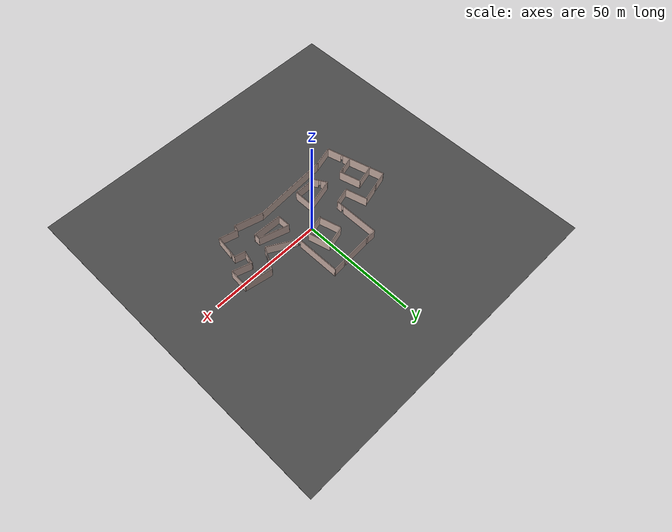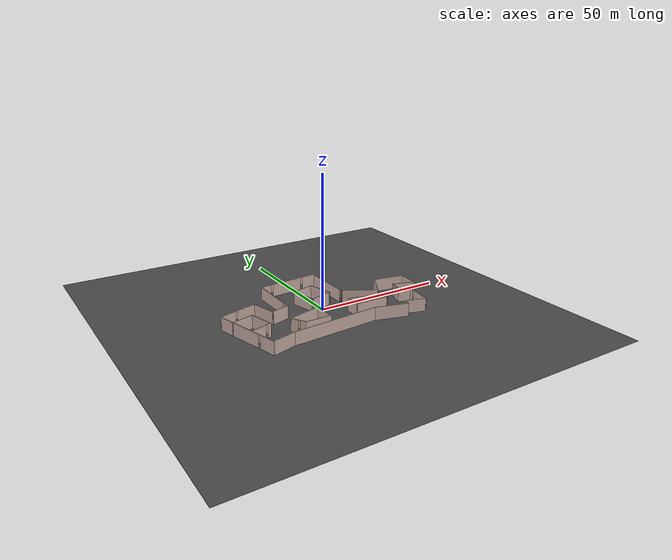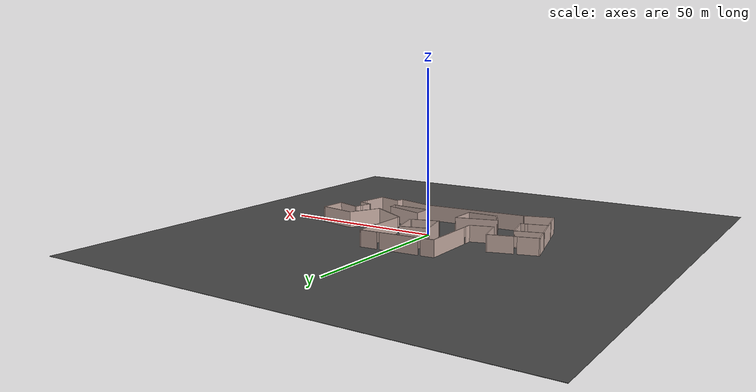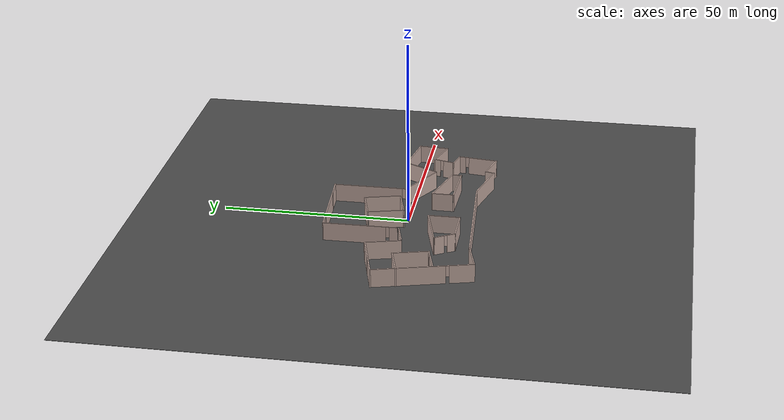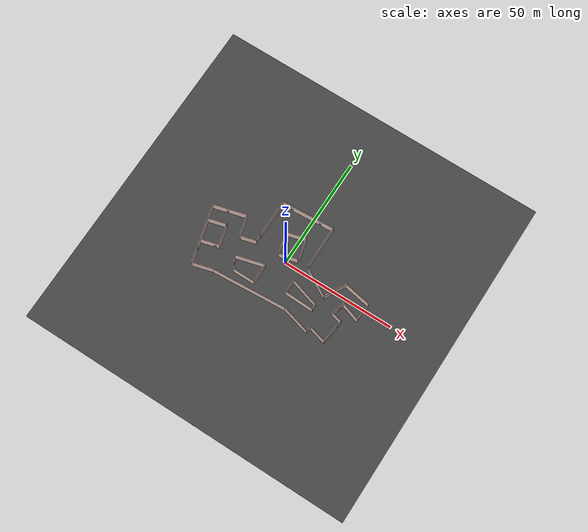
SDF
<?xml version='1.0'?>
<sdf version='1.6'>
  <model name='engineering_2F'>
    <link name='Door_3'>
      <pose frame=''>23.1364 -1.26405 0 0 -0 1.02413</pose>
      <self_collide>0</self_collide>
      <kinematic>0</kinematic>
      <visual name='Door_3_Visual'>
        <pose frame=''>0 0 2.5 0 -0 0</pose>
        <geometry>
          <box>
            <size>3 0.17 5</size>
          </box>
        </geometry>
        <material>
          <script>
            <uri>file://media/materials/scripts/gazebo.material</uri>
            <name>Gazebo/Grey</name>
          </script>
          <ambient>0.3 0.3 0.3 1</ambient>
          <diffuse>0.7 0.7 0.7 1</diffuse>
          <specular>0.01 0.01 0.01 1</specular>
          <emissive>0 0 0 1</emissive>
        </material>
        <cast_shadows>1</cast_shadows>
        <transparency>0</transparency>
      </visual>
      <collision name='Door_3_Collision'>
        <laser_retro>0</laser_retro>
        <max_contacts>10</max_contacts>
        <pose frame=''>0 0 2.5 0 -0 0</pose>
        <geometry>
          <box>
            <size>3 0.17 5</size>
          </box>
        </geometry>
        <surface>
          <friction>
            <ode>
              <mu>1</mu>
              <mu2>1</mu2>
              <fdir1>0 0 0</fdir1>
              <slip1>0</slip1>
              <slip2>0</slip2>
            </ode>
            <torsional>
              <coefficient>1</coefficient>
              <patch_radius>0</patch_radius>
              <surface_radius>0</surface_radius>
              <use_patch_radius>1</use_patch_radius>
              <ode>
                <slip>0</slip>
              </ode>
            </torsional>
          </friction>
          <bounce>
            <restitution_coefficient>0</restitution_coefficient>
            <threshold>1e+06</threshold>
          </bounce>
          <contact>
            <collide_without_contact>0</collide_without_contact>
            <collide_without_contact_bitmask>1</collide_without_contact_bitmask>
            <collide_bitmask>1</collide_bitmask>
            <ode>
              <soft_cfm>0</soft_cfm>
              <soft_erp>0.2</soft_erp>
              <kp>1e+13</kp>
              <kd>1</kd>
              <max_vel>0.01</max_vel>
              <min_depth>0</min_depth>
            </ode>
            <bullet>
              <split_impulse>1</split_impulse>
              <split_impulse_penetration_threshold>-0.01</split_impulse_penetration_threshold>
              <soft_cfm>0</soft_cfm>
              <soft_erp>0.2</soft_erp>
              <kp>1e+13</kp>
              <kd>1</kd>
            </bullet>
          </contact>
        </surface>
      </collision>
    </link>
    <link name='Wall_11'>
      <pose frame=''>28.8708 -5.47569 0 0 0 -1.8326</pose>
      <self_collide>0</self_collide>
      <kinematic>0</kinematic>
      <visual name='Wall_11_Visual_2'>
        <pose frame=''>-0.423205 0 3.5 0 -0 0</pose>
        <geometry>
          <box>
            <size>0.9 0.3 3</size>
          </box>
        </geometry>
        <material>
          <script>
            <uri>file://media/materials/scripts/gazebo.material</uri>
            <name>Gazebo/Grey</name>
          </script>
          <ambient>0.760784 0.662745 0.627451 1</ambient>
          <diffuse>0.7 0.7 0.7 1</diffuse>
          <specular>0.01 0.01 0.01 1</specular>
          <emissive>0 0 0 1</emissive>
        </material>
        <cast_shadows>1</cast_shadows>
        <transparency>0</transparency>
      </visual>
      <visual name='Wall_11_Visual_0'>
        <pose frame=''>-1.8741 0 2.5 0 -0 0</pose>
        <geometry>
          <box>
            <size>2.00179 0.3 5</size>
          </box>
        </geometry>
        <material>
          <script>
            <uri>file://media/materials/scripts/gazebo.material</uri>
            <name>Gazebo/Grey</name>
          </script>
          <ambient>0.760784 0.662745 0.627451 1</ambient>
          <diffuse>0.7 0.7 0.7 1</diffuse>
          <specular>0.01 0.01 0.01 1</specular>
          <emissive>0 0 0 1</emissive>
        </material>
        <cast_shadows>1</cast_shadows>
        <transparency>0</transparency>
      </visual>
      <visual name='Wall_11_Visual_1'>
        <pose frame=''>1.4509 0 2.5 0 -0 0</pose>
        <geometry>
          <box>
            <size>2.84821 0.3 5</size>
          </box>
        </geometry>
        <material>
          <script>
            <uri>file://media/materials/scripts/gazebo.material</uri>
            <name>Gazebo/Grey</name>
          </script>
          <ambient>0.760784 0.662745 0.627451 1</ambient>
          <diffuse>0.7 0.7 0.7 1</diffuse>
          <specular>0.01 0.01 0.01 1</specular>
          <emissive>0 0 0 1</emissive>
        </material>
        <cast_shadows>1</cast_shadows>
        <transparency>0</transparency>
      </visual>
      <collision name='Wall_11_Collision_0'>
        <laser_retro>0</laser_retro>
        <max_contacts>10</max_contacts>
        <pose frame=''>-1.8741 0 2.5 0 -0 0</pose>
        <geometry>
          <box>
            <size>2.00179 0.3 5</size>
          </box>
        </geometry>
        <surface>
          <friction>
            <ode>
              <mu>1</mu>
              <mu2>1</mu2>
              <fdir1>0 0 0</fdir1>
              <slip1>0</slip1>
              <slip2>0</slip2>
            </ode>
            <torsional>
              <coefficient>1</coefficient>
              <patch_radius>0</patch_radius>
              <surface_radius>0</surface_radius>
              <use_patch_radius>1</use_patch_radius>
              <ode>
                <slip>0</slip>
              </ode>
            </torsional>
          </friction>
          <bounce>
            <restitution_coefficient>0</restitution_coefficient>
            <threshold>1e+06</threshold>
          </bounce>
          <contact>
            <collide_without_contact>0</collide_without_contact>
            <collide_without_contact_bitmask>1</collide_without_contact_bitmask>
            <collide_bitmask>1</collide_bitmask>
            <ode>
              <soft_cfm>0</soft_cfm>
              <soft_erp>0.2</soft_erp>
              <kp>1e+13</kp>
              <kd>1</kd>
              <max_vel>0.01</max_vel>
              <min_depth>0</min_depth>
            </ode>
            <bullet>
              <split_impulse>1</split_impulse>
              <split_impulse_penetration_threshold>-0.01</split_impulse_penetration_threshold>
              <soft_cfm>0</soft_cfm>
              <soft_erp>0.2</soft_erp>
              <kp>1e+13</kp>
              <kd>1</kd>
            </bullet>
          </contact>
        </surface>
      </collision>
      <collision name='Wall_11_Collision_2'>
        <laser_retro>0</laser_retro>
        <max_contacts>10</max_contacts>
        <pose frame=''>-0.423205 0 3.5 0 -0 0</pose>
        <geometry>
          <box>
            <size>0.9 0.3 3</size>
          </box>
        </geometry>
        <surface>
          <friction>
            <ode>
              <mu>1</mu>
              <mu2>1</mu2>
              <fdir1>0 0 0</fdir1>
              <slip1>0</slip1>
              <slip2>0</slip2>
            </ode>
            <torsional>
              <coefficient>1</coefficient>
              <patch_radius>0</patch_radius>
              <surface_radius>0</surface_radius>
              <use_patch_radius>1</use_patch_radius>
              <ode>
                <slip>0</slip>
              </ode>
            </torsional>
          </friction>
          <bounce>
            <restitution_coefficient>0</restitution_coefficient>
            <threshold>1e+06</threshold>
          </bounce>
          <contact>
            <collide_without_contact>0</collide_without_contact>
            <collide_without_contact_bitmask>1</collide_without_contact_bitmask>
            <collide_bitmask>1</collide_bitmask>
            <ode>
              <soft_cfm>0</soft_cfm>
              <soft_erp>0.2</soft_erp>
              <kp>1e+13</kp>
              <kd>1</kd>
              <max_vel>0.01</max_vel>
              <min_depth>0</min_depth>
            </ode>
            <bullet>
              <split_impulse>1</split_impulse>
              <split_impulse_penetration_threshold>-0.01</split_impulse_penetration_threshold>
              <soft_cfm>0</soft_cfm>
              <soft_erp>0.2</soft_erp>
              <kp>1e+13</kp>
              <kd>1</kd>
            </bullet>
          </contact>
        </surface>
      </collision>
      <collision name='Wall_11_Collision_1'>
        <laser_retro>0</laser_retro>
        <max_contacts>10</max_contacts>
        <pose frame=''>1.4509 0 2.5 0 -0 0</pose>
        <geometry>
          <box>
            <size>2.84821 0.3 5</size>
          </box>
        </geometry>
        <surface>
          <friction>
            <ode>
              <mu>1</mu>
              <mu2>1</mu2>
              <fdir1>0 0 0</fdir1>
              <slip1>0</slip1>
              <slip2>0</slip2>
            </ode>
            <torsional>
              <coefficient>1</coefficient>
              <patch_radius>0</patch_radius>
              <surface_radius>0</surface_radius>
              <use_patch_radius>1</use_patch_radius>
              <ode>
                <slip>0</slip>
              </ode>
            </torsional>
          </friction>
          <bounce>
            <restitution_coefficient>0</restitution_coefficient>
            <threshold>1e+06</threshold>
          </bounce>
          <contact>
            <collide_without_contact>0</collide_without_contact>
            <collide_without_contact_bitmask>1</collide_without_contact_bitmask>
            <collide_bitmask>1</collide_bitmask>
            <ode>
              <soft_cfm>0</soft_cfm>
              <soft_erp>0.2</soft_erp>
              <kp>1e+13</kp>
              <kd>1</kd>
              <max_vel>0.01</max_vel>
              <min_depth>0</min_depth>
            </ode>
            <bullet>
              <split_impulse>1</split_impulse>
              <split_impulse_penetration_threshold>-0.01</split_impulse_penetration_threshold>
              <soft_cfm>0</soft_cfm>
              <soft_erp>0.2</soft_erp>
              <kp>1e+13</kp>
              <kd>1</kd>
            </bullet>
          </contact>
        </surface>
      </collision>
    </link>
    <link name='Wall_13'>
      <pose frame=''>30.1536 -9.06206 0 0 0 -0.261695</pose>
      <self_collide>0</self_collide>
      <kinematic>0</kinematic>
      <visual name='Wall_13_Visual'>
        <pose frame=''>0 0 2.5 0 -0 0</pose>
        <geometry>
          <box>
            <size>4.8996 0.3 5</size>
          </box>
        </geometry>
        <material>
          <script>
            <uri>file://media/materials/scripts/gazebo.material</uri>
            <name>Gazebo/Grey</name>
          </script>
          <ambient>0.760784 0.662745 0.627451 1</ambient>
          <diffuse>0.7 0.7 0.7 1</diffuse>
          <specular>0.01 0.01 0.01 1</specular>
          <emissive>0 0 0 1</emissive>
        </material>
        <cast_shadows>1</cast_shadows>
        <transparency>0</transparency>
      </visual>
      <collision name='Wall_13_Collision'>
        <laser_retro>0</laser_retro>
        <max_contacts>10</max_contacts>
        <pose frame=''>0 0 2.5 0 -0 0</pose>
        <geometry>
          <box>
            <size>4.8996 0.3 5</size>
          </box>
        </geometry>
        <surface>
          <friction>
            <ode>
              <mu>1</mu>
              <mu2>1</mu2>
              <fdir1>0 0 0</fdir1>
              <slip1>0</slip1>
              <slip2>0</slip2>
            </ode>
            <torsional>
              <coefficient>1</coefficient>
              <patch_radius>0</patch_radius>
              <surface_radius>0</surface_radius>
              <use_patch_radius>1</use_patch_radius>
              <ode>
                <slip>0</slip>
              </ode>
            </torsional>
          </friction>
          <bounce>
            <restitution_coefficient>0</restitution_coefficient>
            <threshold>1e+06</threshold>
          </bounce>
          <contact>
            <collide_without_contact>0</collide_without_contact>
            <collide_without_contact_bitmask>1</collide_without_contact_bitmask>
            <collide_bitmask>1</collide_bitmask>
            <ode>
              <soft_cfm>0</soft_cfm>
              <soft_erp>0.2</soft_erp>
              <kp>1e+13</kp>
              <kd>1</kd>
              <max_vel>0.01</max_vel>
              <min_depth>0</min_depth>
            </ode>
            <bullet>
              <split_impulse>1</split_impulse>
              <split_impulse_penetration_threshold>-0.01</split_impulse_penetration_threshold>
              <soft_cfm>0</soft_cfm>
              <soft_erp>0.2</soft_erp>
              <kp>1e+13</kp>
              <kd>1</kd>
            </bullet>
          </contact>
        </surface>
      </collision>
    </link>
    <link name='Wall_14'>
      <pose frame=''>31.8001 -14.9225 0 0 0 -1.69693</pose>
      <self_collide>0</self_collide>
      <kinematic>0</kinematic>
      <visual name='Wall_14_Visual_0'>
        <pose frame=''>-4.45817 0 2.5 0 -0 0</pose>
        <geometry>
          <box>
            <size>1.83295 0.3 5</size>
          </box>
        </geometry>
        <material>
          <script>
            <uri>file://media/materials/scripts/gazebo.material</uri>
            <name>Gazebo/Grey</name>
          </script>
          <ambient>0.760784 0.662745 0.627451 1</ambient>
          <diffuse>0.7 0.7 0.7 1</diffuse>
          <specular>0.01 0.01 0.01 1</specular>
          <emissive>0 0 0 1</emissive>
        </material>
        <cast_shadows>1</cast_shadows>
        <transparency>0</transparency>
      </visual>
      <visual name='Wall_14_Visual_2'>
        <pose frame=''>-3.0917 0 3.5 0 -0 0</pose>
        <geometry>
          <box>
            <size>0.9 0.3 3</size>
          </box>
        </geometry>
        <material>
          <script>
            <uri>file://media/materials/scripts/gazebo.material</uri>
            <name>Gazebo/Grey</name>
          </script>
          <ambient>0.760784 0.662745 0.627451 1</ambient>
          <diffuse>0.7 0.7 0.7 1</diffuse>
          <specular>0.01 0.01 0.01 1</specular>
          <emissive>0 0 0 1</emissive>
        </material>
        <cast_shadows>1</cast_shadows>
        <transparency>0</transparency>
      </visual>
      <visual name='Wall_14_Visual_1'>
        <pose frame=''>1.36647 0 2.5 0 -0 0</pose>
        <geometry>
          <box>
            <size>8.01634 0.3 5</size>
          </box>
        </geometry>
        <material>
          <script>
            <uri>file://media/materials/scripts/gazebo.material</uri>
            <name>Gazebo/Grey</name>
          </script>
          <ambient>0.760784 0.662745 0.627451 1</ambient>
          <diffuse>0.7 0.7 0.7 1</diffuse>
          <specular>0.01 0.01 0.01 1</specular>
          <emissive>0 0 0 1</emissive>
        </material>
        <cast_shadows>1</cast_shadows>
        <transparency>0</transparency>
      </visual>
      <collision name='Wall_14_Collision_0'>
        <laser_retro>0</laser_retro>
        <max_contacts>10</max_contacts>
        <pose frame=''>-4.45817 0 2.5 0 -0 0</pose>
        <geometry>
          <box>
            <size>1.83295 0.3 5</size>
          </box>
        </geometry>
        <surface>
          <friction>
            <ode>
              <mu>1</mu>
              <mu2>1</mu2>
              <fdir1>0 0 0</fdir1>
              <slip1>0</slip1>
              <slip2>0</slip2>
            </ode>
            <torsional>
              <coefficient>1</coefficient>
              <patch_radius>0</patch_radius>
              <surface_radius>0</surface_radius>
              <use_patch_radius>1</use_patch_radius>
              <ode>
                <slip>0</slip>
              </ode>
            </torsional>
          </friction>
          <bounce>
            <restitution_coefficient>0</restitution_coefficient>
            <threshold>1e+06</threshold>
          </bounce>
          <contact>
            <collide_without_contact>0</collide_without_contact>
            <collide_without_contact_bitmask>1</collide_without_contact_bitmask>
            <collide_bitmask>1</collide_bitmask>
            <ode>
              <soft_cfm>0</soft_cfm>
              <soft_erp>0.2</soft_erp>
              <kp>1e+13</kp>
              <kd>1</kd>
              <max_vel>0.01</max_vel>
              <min_depth>0</min_depth>
            </ode>
            <bullet>
              <split_impulse>1</split_impulse>
              <split_impulse_penetration_threshold>-0.01</split_impulse_penetration_threshold>
              <soft_cfm>0</soft_cfm>
              <soft_erp>0.2</soft_erp>
              <kp>1e+13</kp>
              <kd>1</kd>
            </bullet>
          </contact>
        </surface>
      </collision>
      <collision name='Wall_14_Collision_2'>
        <laser_retro>0</laser_retro>
        <max_contacts>10</max_contacts>
        <pose frame=''>-3.0917 0 3.5 0 -0 0</pose>
        <geometry>
          <box>
            <size>0.9 0.3 3</size>
          </box>
        </geometry>
        <surface>
          <friction>
            <ode>
              <mu>1</mu>
              <mu2>1</mu2>
              <fdir1>0 0 0</fdir1>
              <slip1>0</slip1>
              <slip2>0</slip2>
            </ode>
            <torsional>
              <coefficient>1</coefficient>
              <patch_radius>0</patch_radius>
              <surface_radius>0</surface_radius>
              <use_patch_radius>1</use_patch_radius>
              <ode>
                <slip>0</slip>
              </ode>
            </torsional>
          </friction>
          <bounce>
            <restitution_coefficient>0</restitution_coefficient>
            <threshold>1e+06</threshold>
          </bounce>
          <contact>
            <collide_without_contact>0</collide_without_contact>
            <collide_without_contact_bitmask>1</collide_without_contact_bitmask>
            <collide_bitmask>1</collide_bitmask>
            <ode>
              <soft_cfm>0</soft_cfm>
              <soft_erp>0.2</soft_erp>
              <kp>1e+13</kp>
              <kd>1</kd>
              <max_vel>0.01</max_vel>
              <min_depth>0</min_depth>
            </ode>
            <bullet>
              <split_impulse>1</split_impulse>
              <split_impulse_penetration_threshold>-0.01</split_impulse_penetration_threshold>
              <soft_cfm>0</soft_cfm>
              <soft_erp>0.2</soft_erp>
              <kp>1e+13</kp>
              <kd>1</kd>
            </bullet>
          </contact>
        </surface>
      </collision>
      <collision name='Wall_14_Collision_1'>
        <laser_retro>0</laser_retro>
        <max_contacts>10</max_contacts>
        <pose frame=''>1.36647 0 2.5 0 -0 0</pose>
        <geometry>
          <box>
            <size>8.01634 0.3 5</size>
          </box>
        </geometry>
        <surface>
          <friction>
            <ode>
              <mu>1</mu>
              <mu2>1</mu2>
              <fdir1>0 0 0</fdir1>
              <slip1>0</slip1>
              <slip2>0</slip2>
            </ode>
            <torsional>
              <coefficient>1</coefficient>
              <patch_radius>0</patch_radius>
              <surface_radius>0</surface_radius>
              <use_patch_radius>1</use_patch_radius>
              <ode>
                <slip>0</slip>
              </ode>
            </torsional>
          </friction>
          <bounce>
            <restitution_coefficient>0</restitution_coefficient>
            <threshold>1e+06</threshold>
          </bounce>
          <contact>
            <collide_without_contact>0</collide_without_contact>
            <collide_without_contact_bitmask>1</collide_without_contact_bitmask>
            <collide_bitmask>1</collide_bitmask>
            <ode>
              <soft_cfm>0</soft_cfm>
              <soft_erp>0.2</soft_erp>
              <kp>1e+13</kp>
              <kd>1</kd>
              <max_vel>0.01</max_vel>
              <min_depth>0</min_depth>
            </ode>
            <bullet>
              <split_impulse>1</split_impulse>
              <split_impulse_penetration_threshold>-0.01</split_impulse_penetration_threshold>
              <soft_cfm>0</soft_cfm>
              <soft_erp>0.2</soft_erp>
              <kp>1e+13</kp>
              <kd>1</kd>
            </bullet>
          </contact>
        </surface>
      </collision>
    </link>
    <link name='Wall_15'>
      <pose frame=''>27.3513 -19.0896 0 0 -0 2.87978</pose>
      <self_collide>0</self_collide>
      <kinematic>0</kinematic>
      <visual name='Wall_15_Visual'>
        <pose frame=''>0 0 2.5 0 -0 0</pose>
        <geometry>
          <box>
            <size>8.15012 0.3 5</size>
          </box>
        </geometry>
        <material>
          <script>
            <uri>file://media/materials/scripts/gazebo.material</uri>
            <name>Gazebo/Grey</name>
          </script>
          <ambient>0.760784 0.662745 0.627451 1</ambient>
          <diffuse>0.7 0.7 0.7 1</diffuse>
          <specular>0.01 0.01 0.01 1</specular>
          <emissive>0 0 0 1</emissive>
        </material>
        <cast_shadows>1</cast_shadows>
        <transparency>0</transparency>
      </visual>
      <collision name='Wall_15_Collision'>
        <laser_retro>0</laser_retro>
        <max_contacts>10</max_contacts>
        <pose frame=''>0 0 2.5 0 -0 0</pose>
        <geometry>
          <box>
            <size>8.15012 0.3 5</size>
          </box>
        </geometry>
        <surface>
          <friction>
            <ode>
              <mu>1</mu>
              <mu2>1</mu2>
              <fdir1>0 0 0</fdir1>
              <slip1>0</slip1>
              <slip2>0</slip2>
            </ode>
            <torsional>
              <coefficient>1</coefficient>
              <patch_radius>0</patch_radius>
              <surface_radius>0</surface_radius>
              <use_patch_radius>1</use_patch_radius>
              <ode>
                <slip>0</slip>
              </ode>
            </torsional>
          </friction>
          <bounce>
            <restitution_coefficient>0</restitution_coefficient>
            <threshold>1e+06</threshold>
          </bounce>
          <contact>
            <collide_without_contact>0</collide_without_contact>
            <collide_without_contact_bitmask>1</collide_without_contact_bitmask>
            <collide_bitmask>1</collide_bitmask>
            <ode>
              <soft_cfm>0</soft_cfm>
              <soft_erp>0.2</soft_erp>
              <kp>1e+13</kp>
              <kd>1</kd>
              <max_vel>0.01</max_vel>
              <min_depth>0</min_depth>
            </ode>
            <bullet>
              <split_impulse>1</split_impulse>
              <split_impulse_penetration_threshold>-0.01</split_impulse_penetration_threshold>
              <soft_cfm>0</soft_cfm>
              <soft_erp>0.2</soft_erp>
              <kp>1e+13</kp>
              <kd>1</kd>
            </bullet>
          </contact>
        </surface>
      </collision>
    </link>
    <link name='Wall_16'>
      <pose frame=''>23.2558 -19.2086 0 0 0 -1.83249</pose>
      <self_collide>0</self_collide>
      <kinematic>0</kinematic>
      <visual name='Wall_16_Visual'>
        <pose frame=''>0 0 2.5 0 -0 0</pose>
        <geometry>
          <box>
            <size>2.64983 0.3 5</size>
          </box>
        </geometry>
        <material>
          <script>
            <uri>file://media/materials/scripts/gazebo.material</uri>
            <name>Gazebo/Grey</name>
          </script>
          <ambient>0.760784 0.662745 0.627451 1</ambient>
          <diffuse>0.7 0.7 0.7 1</diffuse>
          <specular>0.01 0.01 0.01 1</specular>
          <emissive>0 0 0 1</emissive>
        </material>
        <cast_shadows>1</cast_shadows>
        <transparency>0</transparency>
      </visual>
      <collision name='Wall_16_Collision'>
        <laser_retro>0</laser_retro>
        <max_contacts>10</max_contacts>
        <pose frame=''>0 0 2.5 0 -0 0</pose>
        <geometry>
          <box>
            <size>2.64983 0.3 5</size>
          </box>
        </geometry>
        <surface>
          <friction>
            <ode>
              <mu>1</mu>
              <mu2>1</mu2>
              <fdir1>0 0 0</fdir1>
              <slip1>0</slip1>
              <slip2>0</slip2>
            </ode>
            <torsional>
              <coefficient>1</coefficient>
              <patch_radius>0</patch_radius>
              <surface_radius>0</surface_radius>
              <use_patch_radius>1</use_patch_radius>
              <ode>
                <slip>0</slip>
              </ode>
            </torsional>
          </friction>
          <bounce>
            <restitution_coefficient>0</restitution_coefficient>
            <threshold>1e+06</threshold>
          </bounce>
          <contact>
            <collide_without_contact>0</collide_without_contact>
            <collide_without_contact_bitmask>1</collide_without_contact_bitmask>
            <collide_bitmask>1</collide_bitmask>
            <ode>
              <soft_cfm>0</soft_cfm>
              <soft_erp>0.2</soft_erp>
              <kp>1e+13</kp>
              <kd>1</kd>
              <max_vel>0.01</max_vel>
              <min_depth>0</min_depth>
            </ode>
            <bullet>
              <split_impulse>1</split_impulse>
              <split_impulse_penetration_threshold>-0.01</split_impulse_penetration_threshold>
              <soft_cfm>0</soft_cfm>
              <soft_erp>0.2</soft_erp>
              <kp>1e+13</kp>
              <kd>1</kd>
            </bullet>
          </contact>
        </surface>
      </collision>
    </link>
    <link name='Wall_17'>
      <pose frame=''>16.8668 -18.7131 0 0 -0 2.87979</pose>
      <self_collide>0</self_collide>
      <kinematic>0</kinematic>
      <visual name='Wall_17_Visual'>
        <pose frame=''>0 0 2.5 0 -0 0</pose>
        <geometry>
          <box>
            <size>12.8998 0.3 5</size>
          </box>
        </geometry>
        <material>
          <script>
            <uri>file://media/materials/scripts/gazebo.material</uri>
            <name>Gazebo/Grey</name>
          </script>
          <ambient>0.760784 0.662745 0.627451 1</ambient>
          <diffuse>0.7 0.7 0.7 1</diffuse>
          <specular>0.01 0.01 0.01 1</specular>
          <emissive>0 0 0 1</emissive>
        </material>
        <cast_shadows>1</cast_shadows>
        <transparency>0</transparency>
      </visual>
      <collision name='Wall_17_Collision'>
        <laser_retro>0</laser_retro>
        <max_contacts>10</max_contacts>
        <pose frame=''>0 0 2.5 0 -0 0</pose>
        <geometry>
          <box>
            <size>12.8998 0.3 5</size>
          </box>
        </geometry>
        <surface>
          <friction>
            <ode>
              <mu>1</mu>
              <mu2>1</mu2>
              <fdir1>0 0 0</fdir1>
              <slip1>0</slip1>
              <slip2>0</slip2>
            </ode>
            <torsional>
              <coefficient>1</coefficient>
              <patch_radius>0</patch_radius>
              <surface_radius>0</surface_radius>
              <use_patch_radius>1</use_patch_radius>
              <ode>
                <slip>0</slip>
              </ode>
            </torsional>
          </friction>
          <bounce>
            <restitution_coefficient>0</restitution_coefficient>
            <threshold>1e+06</threshold>
          </bounce>
          <contact>
            <collide_without_contact>0</collide_without_contact>
            <collide_without_contact_bitmask>1</collide_without_contact_bitmask>
            <collide_bitmask>1</collide_bitmask>
            <ode>
              <soft_cfm>0</soft_cfm>
              <soft_erp>0.2</soft_erp>
              <kp>1e+13</kp>
              <kd>1</kd>
              <max_vel>0.01</max_vel>
              <min_depth>0</min_depth>
            </ode>
            <bullet>
              <split_impulse>1</split_impulse>
              <split_impulse_penetration_threshold>-0.01</split_impulse_penetration_threshold>
              <soft_cfm>0</soft_cfm>
              <soft_erp>0.2</soft_erp>
              <kp>1e+13</kp>
              <kd>1</kd>
            </bullet>
          </contact>
        </surface>
      </collision>
    </link>
    <link name='Wall_21'>
      <pose frame=''>9.15927 11.9128 0 0 -0 1.575</pose>
      <self_collide>0</self_collide>
      <kinematic>0</kinematic>
      <visual name='Wall_21_Visual_2'>
        <pose frame=''>-9.2858 0 3.5 0 -0 0</pose>
        <geometry>
          <box>
            <size>0.9 0.3 3</size>
          </box>
        </geometry>
        <material>
          <script>
            <uri>file://media/materials/scripts/gazebo.material</uri>
            <name>Gazebo/Grey</name>
          </script>
          <ambient>0.760784 0.662745 0.627451 1</ambient>
          <diffuse>0.7 0.7 0.7 1</diffuse>
          <specular>0.01 0.01 0.01 1</specular>
          <emissive>0 0 0 1</emissive>
        </material>
        <cast_shadows>1</cast_shadows>
        <transparency>0</transparency>
      </visual>
      <visual name='Wall_21_Visual_0'>
        <pose frame=''>-9.82244 0 2.5 0 -0 0</pose>
        <geometry>
          <box>
            <size>0.173287 0.3 5</size>
          </box>
        </geometry>
        <material>
          <script>
            <uri>file://media/materials/scripts/gazebo.material</uri>
            <name>Gazebo/Grey</name>
          </script>
          <ambient>0.760784 0.662745 0.627451 1</ambient>
          <diffuse>0.7 0.7 0.7 1</diffuse>
          <specular>0.01 0.01 0.01 1</specular>
          <emissive>0 0 0 1</emissive>
        </material>
        <cast_shadows>1</cast_shadows>
        <transparency>0</transparency>
      </visual>
      <visual name='Wall_21_Visual_1'>
        <pose frame=''>0.536644 0 2.5 0 -0 0</pose>
        <geometry>
          <box>
            <size>18.7449 0.3 5</size>
          </box>
        </geometry>
        <material>
          <script>
            <uri>file://media/materials/scripts/gazebo.material</uri>
            <name>Gazebo/Grey</name>
          </script>
          <ambient>0.760784 0.662745 0.627451 1</ambient>
          <diffuse>0.7 0.7 0.7 1</diffuse>
          <specular>0.01 0.01 0.01 1</specular>
          <emissive>0 0 0 1</emissive>
        </material>
        <cast_shadows>1</cast_shadows>
        <transparency>0</transparency>
      </visual>
      <collision name='Wall_21_Collision_2'>
        <laser_retro>0</laser_retro>
        <max_contacts>10</max_contacts>
        <pose frame=''>-9.2858 0 3.5 0 -0 0</pose>
        <geometry>
          <box>
            <size>0.9 0.3 3</size>
          </box>
        </geometry>
        <surface>
          <friction>
            <ode>
              <mu>1</mu>
              <mu2>1</mu2>
              <fdir1>0 0 0</fdir1>
              <slip1>0</slip1>
              <slip2>0</slip2>
            </ode>
            <torsional>
              <coefficient>1</coefficient>
              <patch_radius>0</patch_radius>
              <surface_radius>0</surface_radius>
              <use_patch_radius>1</use_patch_radius>
              <ode>
                <slip>0</slip>
              </ode>
            </torsional>
          </friction>
          <bounce>
            <restitution_coefficient>0</restitution_coefficient>
            <threshold>1e+06</threshold>
          </bounce>
          <contact>
            <collide_without_contact>0</collide_without_contact>
            <collide_without_contact_bitmask>1</collide_without_contact_bitmask>
            <collide_bitmask>1</collide_bitmask>
            <ode>
              <soft_cfm>0</soft_cfm>
              <soft_erp>0.2</soft_erp>
              <kp>1e+13</kp>
              <kd>1</kd>
              <max_vel>0.01</max_vel>
              <min_depth>0</min_depth>
            </ode>
            <bullet>
              <split_impulse>1</split_impulse>
              <split_impulse_penetration_threshold>-0.01</split_impulse_penetration_threshold>
              <soft_cfm>0</soft_cfm>
              <soft_erp>0.2</soft_erp>
              <kp>1e+13</kp>
              <kd>1</kd>
            </bullet>
          </contact>
        </surface>
      </collision>
      <collision name='Wall_21_Collision_1'>
        <laser_retro>0</laser_retro>
        <max_contacts>10</max_contacts>
        <pose frame=''>0.536644 0 2.5 0 -0 0</pose>
        <geometry>
          <box>
            <size>18.7449 0.3 5</size>
          </box>
        </geometry>
        <surface>
          <friction>
            <ode>
              <mu>1</mu>
              <mu2>1</mu2>
              <fdir1>0 0 0</fdir1>
              <slip1>0</slip1>
              <slip2>0</slip2>
            </ode>
            <torsional>
              <coefficient>1</coefficient>
              <patch_radius>0</patch_radius>
              <surface_radius>0</surface_radius>
              <use_patch_radius>1</use_patch_radius>
              <ode>
                <slip>0</slip>
              </ode>
            </torsional>
          </friction>
          <bounce>
            <restitution_coefficient>0</restitution_coefficient>
            <threshold>1e+06</threshold>
          </bounce>
          <contact>
            <collide_without_contact>0</collide_without_contact>
            <collide_without_contact_bitmask>1</collide_without_contact_bitmask>
            <collide_bitmask>1</collide_bitmask>
            <ode>
              <soft_cfm>0</soft_cfm>
              <soft_erp>0.2</soft_erp>
              <kp>1e+13</kp>
              <kd>1</kd>
              <max_vel>0.01</max_vel>
              <min_depth>0</min_depth>
            </ode>
            <bullet>
              <split_impulse>1</split_impulse>
              <split_impulse_penetration_threshold>-0.01</split_impulse_penetration_threshold>
              <soft_cfm>0</soft_cfm>
              <soft_erp>0.2</soft_erp>
              <kp>1e+13</kp>
              <kd>1</kd>
            </bullet>
          </contact>
        </surface>
      </collision>
      <collision name='Wall_21_Collision_0'>
        <laser_retro>0</laser_retro>
        <max_contacts>10</max_contacts>
        <pose frame=''>-9.82244 0 2.5 0 -0 0</pose>
        <geometry>
          <box>
            <size>0.173287 0.3 5</size>
          </box>
        </geometry>
        <surface>
          <friction>
            <ode>
              <mu>1</mu>
              <mu2>1</mu2>
              <fdir1>0 0 0</fdir1>
              <slip1>0</slip1>
              <slip2>0</slip2>
            </ode>
            <torsional>
              <coefficient>1</coefficient>
              <patch_radius>0</patch_radius>
              <surface_radius>0</surface_radius>
              <use_patch_radius>1</use_patch_radius>
              <ode>
                <slip>0</slip>
              </ode>
            </torsional>
          </friction>
          <bounce>
            <restitution_coefficient>0</restitution_coefficient>
            <threshold>1e+06</threshold>
          </bounce>
          <contact>
            <collide_without_contact>0</collide_without_contact>
            <collide_without_contact_bitmask>1</collide_without_contact_bitmask>
            <collide_bitmask>1</collide_bitmask>
            <ode>
              <soft_cfm>0</soft_cfm>
              <soft_erp>0.2</soft_erp>
              <kp>1e+13</kp>
              <kd>1</kd>
              <max_vel>0.01</max_vel>
              <min_depth>0</min_depth>
            </ode>
            <bullet>
              <split_impulse>1</split_impulse>
              <split_impulse_penetration_threshold>-0.01</split_impulse_penetration_threshold>
              <soft_cfm>0</soft_cfm>
              <soft_erp>0.2</soft_erp>
              <kp>1e+13</kp>
              <kd>1</kd>
            </bullet>
          </contact>
        </surface>
      </collision>
    </link>
    <link name='Wall_23'>
      <pose frame=''>-2.64438 20.8898 0 0 0 -3.08217</pose>
      <self_collide>0</self_collide>
      <kinematic>0</kinematic>
      <visual name='Wall_23_Visual_0'>
        <pose frame=''>-9.13368 0 2.5 0 -0 0</pose>
        <geometry>
          <box>
            <size>5.59954 0.3 5</size>
          </box>
        </geometry>
        <material>
          <script>
            <uri>file://media/materials/scripts/gazebo.material</uri>
            <name>Gazebo/Grey</name>
          </script>
          <ambient>0.760784 0.662745 0.627451 1</ambient>
          <diffuse>0.7 0.7 0.7 1</diffuse>
          <specular>0.01 0.01 0.01 1</specular>
          <emissive>0 0 0 1</emissive>
        </material>
        <cast_shadows>1</cast_shadows>
        <transparency>0</transparency>
      </visual>
      <visual name='Wall_23_Visual_2'>
        <pose frame=''>9.85615 0 2.5 0 -0 0</pose>
        <geometry>
          <box>
            <size>4.15459 0.3 5</size>
          </box>
        </geometry>
        <material>
          <script>
            <uri>file://media/materials/scripts/gazebo.material</uri>
            <name>Gazebo/Grey</name>
          </script>
          <ambient>0.760784 0.662745 0.627451 1</ambient>
          <diffuse>0.7 0.7 0.7 1</diffuse>
          <specular>0.01 0.01 0.01 1</specular>
          <emissive>0 0 0 1</emissive>
        </material>
        <cast_shadows>1</cast_shadows>
        <transparency>0</transparency>
      </visual>
      <visual name='Wall_23_Visual_1'>
        <pose frame=''>0.722472 0 2.5 0 -0 0</pose>
        <geometry>
          <box>
            <size>12.3128 0.3 5</size>
          </box>
        </geometry>
        <material>
          <script>
            <uri>file://media/materials/scripts/gazebo.material</uri>
            <name>Gazebo/Grey</name>
          </script>
          <ambient>0.760784 0.662745 0.627451 1</ambient>
          <diffuse>0.7 0.7 0.7 1</diffuse>
          <specular>0.01 0.01 0.01 1</specular>
          <emissive>0 0 0 1</emissive>
        </material>
        <cast_shadows>1</cast_shadows>
        <transparency>0</transparency>
      </visual>
      <visual name='Wall_23_Visual_3'>
        <pose frame=''>-5.88391 0 3.5 0 -0 0</pose>
        <geometry>
          <box>
            <size>0.9 0.3 3</size>
          </box>
        </geometry>
        <material>
          <script>
            <uri>file://media/materials/scripts/gazebo.material</uri>
            <name>Gazebo/Grey</name>
          </script>
          <ambient>0.760784 0.662745 0.627451 1</ambient>
          <diffuse>0.7 0.7 0.7 1</diffuse>
          <specular>0.01 0.01 0.01 1</specular>
          <emissive>0 0 0 1</emissive>
        </material>
        <cast_shadows>1</cast_shadows>
        <transparency>0</transparency>
      </visual>
      <visual name='Wall_23_Visual_4'>
        <pose frame=''>7.32885 0 3.5 0 -0 0</pose>
        <geometry>
          <box>
            <size>0.9 0.3 3</size>
          </box>
        </geometry>
        <material>
          <script>
            <uri>file://media/materials/scripts/gazebo.material</uri>
            <name>Gazebo/Grey</name>
          </script>
          <ambient>0.760784 0.662745 0.627451 1</ambient>
          <diffuse>0.7 0.7 0.7 1</diffuse>
          <specular>0.01 0.01 0.01 1</specular>
          <emissive>0 0 0 1</emissive>
        </material>
        <cast_shadows>1</cast_shadows>
        <transparency>0</transparency>
      </visual>
      <collision name='Wall_23_Collision_3'>
        <laser_retro>0</laser_retro>
        <max_contacts>10</max_contacts>
        <pose frame=''>-5.88391 0 3.5 0 -0 0</pose>
        <geometry>
          <box>
            <size>0.9 0.3 3</size>
          </box>
        </geometry>
        <surface>
          <friction>
            <ode>
              <mu>1</mu>
              <mu2>1</mu2>
              <fdir1>0 0 0</fdir1>
              <slip1>0</slip1>
              <slip2>0</slip2>
            </ode>
            <torsional>
              <coefficient>1</coefficient>
              <patch_radius>0</patch_radius>
              <surface_radius>0</surface_radius>
              <use_patch_radius>1</use_patch_radius>
              <ode>
                <slip>0</slip>
              </ode>
            </torsional>
          </friction>
          <bounce>
            <restitution_coefficient>0</restitution_coefficient>
            <threshold>1e+06</threshold>
          </bounce>
          <contact>
            <collide_without_contact>0</collide_without_contact>
            <collide_without_contact_bitmask>1</collide_without_contact_bitmask>
            <collide_bitmask>1</collide_bitmask>
            <ode>
              <soft_cfm>0</soft_cfm>
              <soft_erp>0.2</soft_erp>
              <kp>1e+13</kp>
              <kd>1</kd>
              <max_vel>0.01</max_vel>
              <min_depth>0</min_depth>
            </ode>
            <bullet>
              <split_impulse>1</split_impulse>
              <split_impulse_penetration_threshold>-0.01</split_impulse_penetration_threshold>
              <soft_cfm>0</soft_cfm>
              <soft_erp>0.2</soft_erp>
              <kp>1e+13</kp>
              <kd>1</kd>
            </bullet>
          </contact>
        </surface>
      </collision>
      <collision name='Wall_23_Collision_1'>
        <laser_retro>0</laser_retro>
        <max_contacts>10</max_contacts>
        <pose frame=''>0.722472 0 2.5 0 -0 0</pose>
        <geometry>
          <box>
            <size>12.3128 0.3 5</size>
          </box>
        </geometry>
        <surface>
          <friction>
            <ode>
              <mu>1</mu>
              <mu2>1</mu2>
              <fdir1>0 0 0</fdir1>
              <slip1>0</slip1>
              <slip2>0</slip2>
            </ode>
            <torsional>
              <coefficient>1</coefficient>
              <patch_radius>0</patch_radius>
              <surface_radius>0</surface_radius>
              <use_patch_radius>1</use_patch_radius>
              <ode>
                <slip>0</slip>
              </ode>
            </torsional>
          </friction>
          <bounce>
            <restitution_coefficient>0</restitution_coefficient>
            <threshold>1e+06</threshold>
          </bounce>
          <contact>
            <collide_without_contact>0</collide_without_contact>
            <collide_without_contact_bitmask>1</collide_without_contact_bitmask>
            <collide_bitmask>1</collide_bitmask>
            <ode>
              <soft_cfm>0</soft_cfm>
              <soft_erp>0.2</soft_erp>
              <kp>1e+13</kp>
              <kd>1</kd>
              <max_vel>0.01</max_vel>
              <min_depth>0</min_depth>
            </ode>
            <bullet>
              <split_impulse>1</split_impulse>
              <split_impulse_penetration_threshold>-0.01</split_impulse_penetration_threshold>
              <soft_cfm>0</soft_cfm>
              <soft_erp>0.2</soft_erp>
              <kp>1e+13</kp>
              <kd>1</kd>
            </bullet>
          </contact>
        </surface>
      </collision>
      <collision name='Wall_23_Collision_2'>
        <laser_retro>0</laser_retro>
        <max_contacts>10</max_contacts>
        <pose frame=''>9.85615 0 2.5 0 -0 0</pose>
        <geometry>
          <box>
            <size>4.15459 0.3 5</size>
          </box>
        </geometry>
        <surface>
          <friction>
            <ode>
              <mu>1</mu>
              <mu2>1</mu2>
              <fdir1>0 0 0</fdir1>
              <slip1>0</slip1>
              <slip2>0</slip2>
            </ode>
            <torsional>
              <coefficient>1</coefficient>
              <patch_radius>0</patch_radius>
              <surface_radius>0</surface_radius>
              <use_patch_radius>1</use_patch_radius>
              <ode>
                <slip>0</slip>
              </ode>
            </torsional>
          </friction>
          <bounce>
            <restitution_coefficient>0</restitution_coefficient>
            <threshold>1e+06</threshold>
          </bounce>
          <contact>
            <collide_without_contact>0</collide_without_contact>
            <collide_without_contact_bitmask>1</collide_without_contact_bitmask>
            <collide_bitmask>1</collide_bitmask>
            <ode>
              <soft_cfm>0</soft_cfm>
              <soft_erp>0.2</soft_erp>
              <kp>1e+13</kp>
              <kd>1</kd>
              <max_vel>0.01</max_vel>
              <min_depth>0</min_depth>
            </ode>
            <bullet>
              <split_impulse>1</split_impulse>
              <split_impulse_penetration_threshold>-0.01</split_impulse_penetration_threshold>
              <soft_cfm>0</soft_cfm>
              <soft_erp>0.2</soft_erp>
              <kp>1e+13</kp>
              <kd>1</kd>
            </bullet>
          </contact>
        </surface>
      </collision>
      <collision name='Wall_23_Collision_0'>
        <laser_retro>0</laser_retro>
        <max_contacts>10</max_contacts>
        <pose frame=''>-9.13368 0 2.5 0 -0 0</pose>
        <geometry>
          <box>
            <size>5.59954 0.3 5</size>
          </box>
        </geometry>
        <surface>
          <friction>
            <ode>
              <mu>1</mu>
              <mu2>1</mu2>
              <fdir1>0 0 0</fdir1>
              <slip1>0</slip1>
              <slip2>0</slip2>
            </ode>
            <torsional>
              <coefficient>1</coefficient>
              <patch_radius>0</patch_radius>
              <surface_radius>0</surface_radius>
              <use_patch_radius>1</use_patch_radius>
              <ode>
                <slip>0</slip>
              </ode>
            </torsional>
          </friction>
          <bounce>
            <restitution_coefficient>0</restitution_coefficient>
            <threshold>1e+06</threshold>
          </bounce>
          <contact>
            <collide_without_contact>0</collide_without_contact>
            <collide_without_contact_bitmask>1</collide_without_contact_bitmask>
            <collide_bitmask>1</collide_bitmask>
            <ode>
              <soft_cfm>0</soft_cfm>
              <soft_erp>0.2</soft_erp>
              <kp>1e+13</kp>
              <kd>1</kd>
              <max_vel>0.01</max_vel>
              <min_depth>0</min_depth>
            </ode>
            <bullet>
              <split_impulse>1</split_impulse>
              <split_impulse_penetration_threshold>-0.01</split_impulse_penetration_threshold>
              <soft_cfm>0</soft_cfm>
              <soft_erp>0.2</soft_erp>
              <kp>1e+13</kp>
              <kd>1</kd>
            </bullet>
          </contact>
        </surface>
      </collision>
      <collision name='Wall_23_Collision_4'>
        <laser_retro>0</laser_retro>
        <max_contacts>10</max_contacts>
        <pose frame=''>7.32885 0 3.5 0 -0 0</pose>
        <geometry>
          <box>
            <size>0.9 0.3 3</size>
          </box>
        </geometry>
        <surface>
          <friction>
            <ode>
              <mu>1</mu>
              <mu2>1</mu2>
              <fdir1>0 0 0</fdir1>
              <slip1>0</slip1>
              <slip2>0</slip2>
            </ode>
            <torsional>
              <coefficient>1</coefficient>
              <patch_radius>0</patch_radius>
              <surface_radius>0</surface_radius>
              <use_patch_radius>1</use_patch_radius>
              <ode>
                <slip>0</slip>
              </ode>
            </torsional>
          </friction>
          <bounce>
            <restitution_coefficient>0</restitution_coefficient>
            <threshold>1e+06</threshold>
          </bounce>
          <contact>
            <collide_without_contact>0</collide_without_contact>
            <collide_without_contact_bitmask>1</collide_without_contact_bitmask>
            <collide_bitmask>1</collide_bitmask>
            <ode>
              <soft_cfm>0</soft_cfm>
              <soft_erp>0.2</soft_erp>
              <kp>1e+13</kp>
              <kd>1</kd>
              <max_vel>0.01</max_vel>
              <min_depth>0</min_depth>
            </ode>
            <bullet>
              <split_impulse>1</split_impulse>
              <split_impulse_penetration_threshold>-0.01</split_impulse_penetration_threshold>
              <soft_cfm>0</soft_cfm>
              <soft_erp>0.2</soft_erp>
              <kp>1e+13</kp>
              <kd>1</kd>
            </bullet>
          </contact>
        </surface>
      </collision>
    </link>
    <link name='Wall_25'>
      <pose frame=''>-14.3661 10.3901 0 0 0 -1.56658</pose>
      <self_collide>0</self_collide>
      <kinematic>0</kinematic>
      <visual name='Wall_25_Visual_1'>
        <pose frame=''>8.7734 0 2.5 0 -0 0</pose>
        <geometry>
          <box>
            <size>2.18873 0.3 5</size>
          </box>
        </geometry>
        <material>
          <script>
            <uri>file://media/materials/scripts/gazebo.material</uri>
            <name>Gazebo/Grey</name>
          </script>
          <ambient>0.760784 0.662745 0.627451 1</ambient>
          <diffuse>0.7 0.7 0.7 1</diffuse>
          <specular>0.01 0.01 0.01 1</specular>
          <emissive>0 0 0 1</emissive>
        </material>
        <cast_shadows>1</cast_shadows>
        <transparency>0</transparency>
      </visual>
      <visual name='Wall_25_Visual_0'>
        <pose frame=''>-1.54436 0 2.5 0 -0 0</pose>
        <geometry>
          <box>
            <size>16.6468 0.3 5</size>
          </box>
        </geometry>
        <material>
          <script>
            <uri>file://media/materials/scripts/gazebo.material</uri>
            <name>Gazebo/Grey</name>
          </script>
          <ambient>0.760784 0.662745 0.627451 1</ambient>
          <diffuse>0.7 0.7 0.7 1</diffuse>
          <specular>0.01 0.01 0.01 1</specular>
          <emissive>0 0 0 1</emissive>
        </material>
        <cast_shadows>1</cast_shadows>
        <transparency>0</transparency>
      </visual>
      <visual name='Wall_25_Visual_2'>
        <pose frame=''>7.22904 0 3.5 0 -0 0</pose>
        <geometry>
          <box>
            <size>0.9 0.3 3</size>
          </box>
        </geometry>
        <material>
          <script>
            <uri>file://media/materials/scripts/gazebo.material</uri>
            <name>Gazebo/Grey</name>
          </script>
          <ambient>0.760784 0.662745 0.627451 1</ambient>
          <diffuse>0.7 0.7 0.7 1</diffuse>
          <specular>0.01 0.01 0.01 1</specular>
          <emissive>0 0 0 1</emissive>
        </material>
        <cast_shadows>1</cast_shadows>
        <transparency>0</transparency>
      </visual>
      <collision name='Wall_25_Collision_2'>
        <laser_retro>0</laser_retro>
        <max_contacts>10</max_contacts>
        <pose frame=''>7.22904 0 3.5 0 -0 0</pose>
        <geometry>
          <box>
            <size>0.9 0.3 3</size>
          </box>
        </geometry>
        <surface>
          <friction>
            <ode>
              <mu>1</mu>
              <mu2>1</mu2>
              <fdir1>0 0 0</fdir1>
              <slip1>0</slip1>
              <slip2>0</slip2>
            </ode>
            <torsional>
              <coefficient>1</coefficient>
              <patch_radius>0</patch_radius>
              <surface_radius>0</surface_radius>
              <use_patch_radius>1</use_patch_radius>
              <ode>
                <slip>0</slip>
              </ode>
            </torsional>
          </friction>
          <bounce>
            <restitution_coefficient>0</restitution_coefficient>
            <threshold>1e+06</threshold>
          </bounce>
          <contact>
            <collide_without_contact>0</collide_without_contact>
            <collide_without_contact_bitmask>1</collide_without_contact_bitmask>
            <collide_bitmask>1</collide_bitmask>
            <ode>
              <soft_cfm>0</soft_cfm>
              <soft_erp>0.2</soft_erp>
              <kp>1e+13</kp>
              <kd>1</kd>
              <max_vel>0.01</max_vel>
              <min_depth>0</min_depth>
            </ode>
            <bullet>
              <split_impulse>1</split_impulse>
              <split_impulse_penetration_threshold>-0.01</split_impulse_penetration_threshold>
              <soft_cfm>0</soft_cfm>
              <soft_erp>0.2</soft_erp>
              <kp>1e+13</kp>
              <kd>1</kd>
            </bullet>
          </contact>
        </surface>
      </collision>
      <collision name='Wall_25_Collision_1'>
        <laser_retro>0</laser_retro>
        <max_contacts>10</max_contacts>
        <pose frame=''>8.7734 0 2.5 0 -0 0</pose>
        <geometry>
          <box>
            <size>2.18873 0.3 5</size>
          </box>
        </geometry>
        <surface>
          <friction>
            <ode>
              <mu>1</mu>
              <mu2>1</mu2>
              <fdir1>0 0 0</fdir1>
              <slip1>0</slip1>
              <slip2>0</slip2>
            </ode>
            <torsional>
              <coefficient>1</coefficient>
              <patch_radius>0</patch_radius>
              <surface_radius>0</surface_radius>
              <use_patch_radius>1</use_patch_radius>
              <ode>
                <slip>0</slip>
              </ode>
            </torsional>
          </friction>
          <bounce>
            <restitution_coefficient>0</restitution_coefficient>
            <threshold>1e+06</threshold>
          </bounce>
          <contact>
            <collide_without_contact>0</collide_without_contact>
            <collide_without_contact_bitmask>1</collide_without_contact_bitmask>
            <collide_bitmask>1</collide_bitmask>
            <ode>
              <soft_cfm>0</soft_cfm>
              <soft_erp>0.2</soft_erp>
              <kp>1e+13</kp>
              <kd>1</kd>
              <max_vel>0.01</max_vel>
              <min_depth>0</min_depth>
            </ode>
            <bullet>
              <split_impulse>1</split_impulse>
              <split_impulse_penetration_threshold>-0.01</split_impulse_penetration_threshold>
              <soft_cfm>0</soft_cfm>
              <soft_erp>0.2</soft_erp>
              <kp>1e+13</kp>
              <kd>1</kd>
            </bullet>
          </contact>
        </surface>
      </collision>
      <collision name='Wall_25_Collision_0'>
        <laser_retro>0</laser_retro>
        <max_contacts>10</max_contacts>
        <pose frame=''>-1.54436 0 2.5 0 -0 0</pose>
        <geometry>
          <box>
            <size>16.6468 0.3 5</size>
          </box>
        </geometry>
        <surface>
          <friction>
            <ode>
              <mu>1</mu>
              <mu2>1</mu2>
              <fdir1>0 0 0</fdir1>
              <slip1>0</slip1>
              <slip2>0</slip2>
            </ode>
            <torsional>
              <coefficient>1</coefficient>
              <patch_radius>0</patch_radius>
              <surface_radius>0</surface_radius>
              <use_patch_radius>1</use_patch_radius>
              <ode>
                <slip>0</slip>
              </ode>
            </torsional>
          </friction>
          <bounce>
            <restitution_coefficient>0</restitution_coefficient>
            <threshold>1e+06</threshold>
          </bounce>
          <contact>
            <collide_without_contact>0</collide_without_contact>
            <collide_without_contact_bitmask>1</collide_without_contact_bitmask>
            <collide_bitmask>1</collide_bitmask>
            <ode>
              <soft_cfm>0</soft_cfm>
              <soft_erp>0.2</soft_erp>
              <kp>1e+13</kp>
              <kd>1</kd>
              <max_vel>0.01</max_vel>
              <min_depth>0</min_depth>
            </ode>
            <bullet>
              <split_impulse>1</split_impulse>
              <split_impulse_penetration_threshold>-0.01</split_impulse_penetration_threshold>
              <soft_cfm>0</soft_cfm>
              <soft_erp>0.2</soft_erp>
              <kp>1e+13</kp>
              <kd>1</kd>
            </bullet>
          </contact>
        </surface>
      </collision>
    </link>
    <link name='Wall_31'>
      <pose frame=''>-30.9302 5.46088 0 0 0 -2.87977</pose>
      <self_collide>0</self_collide>
      <kinematic>0</kinematic>
      <visual name='Wall_31_Visual_2'>
        <pose frame=''>0.628976 0 3.5 0 -0 0</pose>
        <geometry>
          <box>
            <size>0.9 0.3 3</size>
          </box>
        </geometry>
        <material>
          <script>
            <uri>file://media/materials/scripts/gazebo.material</uri>
            <name>Gazebo/Grey</name>
          </script>
          <ambient>0.760784 0.662745 0.627451 1</ambient>
          <diffuse>0.7 0.7 0.7 1</diffuse>
          <specular>0.01 0.01 0.01 1</specular>
          <emissive>0 0 0 1</emissive>
        </material>
        <cast_shadows>1</cast_shadows>
        <transparency>0</transparency>
      </visual>
      <visual name='Wall_31_Visual_0'>
        <pose frame=''>-3.63546 0 2.5 0 -0 0</pose>
        <geometry>
          <box>
            <size>7.62887 0.3 5</size>
          </box>
        </geometry>
        <material>
          <script>
            <uri>file://media/materials/scripts/gazebo.material</uri>
            <name>Gazebo/Grey</name>
          </script>
          <ambient>0.760784 0.662745 0.627451 1</ambient>
          <diffuse>0.7 0.7 0.7 1</diffuse>
          <specular>0.01 0.01 0.01 1</specular>
          <emissive>0 0 0 1</emissive>
        </material>
        <cast_shadows>1</cast_shadows>
        <transparency>0</transparency>
      </visual>
      <visual name='Wall_31_Visual_1'>
        <pose frame=''>4.26443 0 2.5 0 -0 0</pose>
        <geometry>
          <box>
            <size>6.37091 0.3 5</size>
          </box>
        </geometry>
        <material>
          <script>
            <uri>file://media/materials/scripts/gazebo.material</uri>
            <name>Gazebo/Grey</name>
          </script>
          <ambient>0.760784 0.662745 0.627451 1</ambient>
          <diffuse>0.7 0.7 0.7 1</diffuse>
          <specular>0.01 0.01 0.01 1</specular>
          <emissive>0 0 0 1</emissive>
        </material>
        <cast_shadows>1</cast_shadows>
        <transparency>0</transparency>
      </visual>
      <collision name='Wall_31_Collision_2'>
        <laser_retro>0</laser_retro>
        <max_contacts>10</max_contacts>
        <pose frame=''>0.628976 0 3.5 0 -0 0</pose>
        <geometry>
          <box>
            <size>0.9 0.3 3</size>
          </box>
        </geometry>
        <surface>
          <friction>
            <ode>
              <mu>1</mu>
              <mu2>1</mu2>
              <fdir1>0 0 0</fdir1>
              <slip1>0</slip1>
              <slip2>0</slip2>
            </ode>
            <torsional>
              <coefficient>1</coefficient>
              <patch_radius>0</patch_radius>
              <surface_radius>0</surface_radius>
              <use_patch_radius>1</use_patch_radius>
              <ode>
                <slip>0</slip>
              </ode>
            </torsional>
          </friction>
          <bounce>
            <restitution_coefficient>0</restitution_coefficient>
            <threshold>1e+06</threshold>
          </bounce>
          <contact>
            <collide_without_contact>0</collide_without_contact>
            <collide_without_contact_bitmask>1</collide_without_contact_bitmask>
            <collide_bitmask>1</collide_bitmask>
            <ode>
              <soft_cfm>0</soft_cfm>
              <soft_erp>0.2</soft_erp>
              <kp>1e+13</kp>
              <kd>1</kd>
              <max_vel>0.01</max_vel>
              <min_depth>0</min_depth>
            </ode>
            <bullet>
              <split_impulse>1</split_impulse>
              <split_impulse_penetration_threshold>-0.01</split_impulse_penetration_threshold>
              <soft_cfm>0</soft_cfm>
              <soft_erp>0.2</soft_erp>
              <kp>1e+13</kp>
              <kd>1</kd>
            </bullet>
          </contact>
        </surface>
      </collision>
      <collision name='Wall_31_Collision_1'>
        <laser_retro>0</laser_retro>
        <max_contacts>10</max_contacts>
        <pose frame=''>4.26443 0 2.5 0 -0 0</pose>
        <geometry>
          <box>
            <size>6.37091 0.3 5</size>
          </box>
        </geometry>
        <surface>
          <friction>
            <ode>
              <mu>1</mu>
              <mu2>1</mu2>
              <fdir1>0 0 0</fdir1>
              <slip1>0</slip1>
              <slip2>0</slip2>
            </ode>
            <torsional>
              <coefficient>1</coefficient>
              <patch_radius>0</patch_radius>
              <surface_radius>0</surface_radius>
              <use_patch_radius>1</use_patch_radius>
              <ode>
                <slip>0</slip>
              </ode>
            </torsional>
          </friction>
          <bounce>
            <restitution_coefficient>0</restitution_coefficient>
            <threshold>1e+06</threshold>
          </bounce>
          <contact>
            <collide_without_contact>0</collide_without_contact>
            <collide_without_contact_bitmask>1</collide_without_contact_bitmask>
            <collide_bitmask>1</collide_bitmask>
            <ode>
              <soft_cfm>0</soft_cfm>
              <soft_erp>0.2</soft_erp>
              <kp>1e+13</kp>
              <kd>1</kd>
              <max_vel>0.01</max_vel>
              <min_depth>0</min_depth>
            </ode>
            <bullet>
              <split_impulse>1</split_impulse>
              <split_impulse_penetration_threshold>-0.01</split_impulse_penetration_threshold>
              <soft_cfm>0</soft_cfm>
              <soft_erp>0.2</soft_erp>
              <kp>1e+13</kp>
              <kd>1</kd>
            </bullet>
          </contact>
        </surface>
      </collision>
      <collision name='Wall_31_Collision_0'>
        <laser_retro>0</laser_retro>
        <max_contacts>10</max_contacts>
        <pose frame=''>-3.63546 0 2.5 0 -0 0</pose>
        <geometry>
          <box>
            <size>7.62887 0.3 5</size>
          </box>
        </geometry>
        <surface>
          <friction>
            <ode>
              <mu>1</mu>
              <mu2>1</mu2>
              <fdir1>0 0 0</fdir1>
              <slip1>0</slip1>
              <slip2>0</slip2>
            </ode>
            <torsional>
              <coefficient>1</coefficient>
              <patch_radius>0</patch_radius>
              <surface_radius>0</surface_radius>
              <use_patch_radius>1</use_patch_radius>
              <ode>
                <slip>0</slip>
              </ode>
            </torsional>
          </friction>
          <bounce>
            <restitution_coefficient>0</restitution_coefficient>
            <threshold>1e+06</threshold>
          </bounce>
          <contact>
            <collide_without_contact>0</collide_without_contact>
            <collide_without_contact_bitmask>1</collide_without_contact_bitmask>
            <collide_bitmask>1</collide_bitmask>
            <ode>
              <soft_cfm>0</soft_cfm>
              <soft_erp>0.2</soft_erp>
              <kp>1e+13</kp>
              <kd>1</kd>
              <max_vel>0.01</max_vel>
              <min_depth>0</min_depth>
            </ode>
            <bullet>
              <split_impulse>1</split_impulse>
              <split_impulse_penetration_threshold>-0.01</split_impulse_penetration_threshold>
              <soft_cfm>0</soft_cfm>
              <soft_erp>0.2</soft_erp>
              <kp>1e+13</kp>
              <kd>1</kd>
            </bullet>
          </contact>
        </surface>
      </collision>
    </link>
    <link name='Wall_4'>
      <pose frame=''>32.0256 3.41396 0 0 -0 2.96431</pose>
      <self_collide>0</self_collide>
      <kinematic>0</kinematic>
      <visual name='Wall_4_Visual'>
        <pose frame=''>0 0 2.5 0 -0 0</pose>
        <geometry>
          <box>
            <size>12.2839 0.3 5</size>
          </box>
        </geometry>
        <material>
          <script>
            <uri>file://media/materials/scripts/gazebo.material</uri>
            <name>Gazebo/Grey</name>
          </script>
          <ambient>0.760784 0.662745 0.627451 1</ambient>
          <diffuse>0.7 0.7 0.7 1</diffuse>
          <specular>0.01 0.01 0.01 1</specular>
          <emissive>0 0 0 1</emissive>
        </material>
        <cast_shadows>1</cast_shadows>
        <transparency>0</transparency>
      </visual>
      <collision name='Wall_4_Collision'>
        <laser_retro>0</laser_retro>
        <max_contacts>10</max_contacts>
        <pose frame=''>0 0 2.5 0 -0 0</pose>
        <geometry>
          <box>
            <size>12.2839 0.3 5</size>
          </box>
        </geometry>
        <surface>
          <friction>
            <ode>
              <mu>1</mu>
              <mu2>1</mu2>
              <fdir1>0 0 0</fdir1>
              <slip1>0</slip1>
              <slip2>0</slip2>
            </ode>
            <torsional>
              <coefficient>1</coefficient>
              <patch_radius>0</patch_radius>
              <surface_radius>0</surface_radius>
              <use_patch_radius>1</use_patch_radius>
              <ode>
                <slip>0</slip>
              </ode>
            </torsional>
          </friction>
          <bounce>
            <restitution_coefficient>0</restitution_coefficient>
            <threshold>1e+06</threshold>
          </bounce>
          <contact>
            <collide_without_contact>0</collide_without_contact>
            <collide_without_contact_bitmask>1</collide_without_contact_bitmask>
            <collide_bitmask>1</collide_bitmask>
            <ode>
              <soft_cfm>0</soft_cfm>
              <soft_erp>0.2</soft_erp>
              <kp>1e+13</kp>
              <kd>1</kd>
              <max_vel>0.01</max_vel>
              <min_depth>0</min_depth>
            </ode>
            <bullet>
              <split_impulse>1</split_impulse>
              <split_impulse_penetration_threshold>-0.01</split_impulse_penetration_threshold>
              <soft_cfm>0</soft_cfm>
              <soft_erp>0.2</soft_erp>
              <kp>1e+13</kp>
              <kd>1</kd>
            </bullet>
          </contact>
        </surface>
      </collision>
    </link>
    <link name='Wall_40'>
      <pose frame=''>-34.6037 -9.03362 0 0 0 -1.309</pose>
      <self_collide>0</self_collide>
      <kinematic>0</kinematic>
      <visual name='Wall_40_Visual_2'>
        <pose frame=''>6.30714 0 3.5 0 -0 0</pose>
        <geometry>
          <box>
            <size>0.9 0.3 3</size>
          </box>
        </geometry>
        <material>
          <script>
            <uri>file://media/materials/scripts/gazebo.material</uri>
            <name>Gazebo/Grey</name>
          </script>
          <ambient>0.760784 0.662745 0.627451 1</ambient>
          <diffuse>0.7 0.7 0.7 1</diffuse>
          <specular>0.01 0.01 0.01 1</specular>
          <emissive>0 0 0 1</emissive>
        </material>
        <cast_shadows>1</cast_shadows>
        <transparency>0</transparency>
      </visual>
      <visual name='Wall_40_Visual_1'>
        <pose frame=''>9.97844 0 2.5 0 -0 0</pose>
        <geometry>
          <box>
            <size>6.4426 0.3 5</size>
          </box>
        </geometry>
        <material>
          <script>
            <uri>file://media/materials/scripts/gazebo.material</uri>
            <name>Gazebo/Grey</name>
          </script>
          <ambient>0.760784 0.662745 0.627451 1</ambient>
          <diffuse>0.7 0.7 0.7 1</diffuse>
          <specular>0.01 0.01 0.01 1</specular>
          <emissive>0 0 0 1</emissive>
        </material>
        <cast_shadows>1</cast_shadows>
        <transparency>0</transparency>
      </visual>
      <visual name='Wall_40_Visual_0'>
        <pose frame=''>-3.6713 0 2.5 0 -0 0</pose>
        <geometry>
          <box>
            <size>19.0569 0.3 5</size>
          </box>
        </geometry>
        <material>
          <script>
            <uri>file://media/materials/scripts/gazebo.material</uri>
            <name>Gazebo/Grey</name>
          </script>
          <ambient>0.760784 0.662745 0.627451 1</ambient>
          <diffuse>0.7 0.7 0.7 1</diffuse>
          <specular>0.01 0.01 0.01 1</specular>
          <emissive>0 0 0 1</emissive>
        </material>
        <cast_shadows>1</cast_shadows>
        <transparency>0</transparency>
      </visual>
      <collision name='Wall_40_Collision_1'>
        <laser_retro>0</laser_retro>
        <max_contacts>10</max_contacts>
        <pose frame=''>9.97844 0 2.5 0 -0 0</pose>
        <geometry>
          <box>
            <size>6.4426 0.3 5</size>
          </box>
        </geometry>
        <surface>
          <friction>
            <ode>
              <mu>1</mu>
              <mu2>1</mu2>
              <fdir1>0 0 0</fdir1>
              <slip1>0</slip1>
              <slip2>0</slip2>
            </ode>
            <torsional>
              <coefficient>1</coefficient>
              <patch_radius>0</patch_radius>
              <surface_radius>0</surface_radius>
              <use_patch_radius>1</use_patch_radius>
              <ode>
                <slip>0</slip>
              </ode>
            </torsional>
          </friction>
          <bounce>
            <restitution_coefficient>0</restitution_coefficient>
            <threshold>1e+06</threshold>
          </bounce>
          <contact>
            <collide_without_contact>0</collide_without_contact>
            <collide_without_contact_bitmask>1</collide_without_contact_bitmask>
            <collide_bitmask>1</collide_bitmask>
            <ode>
              <soft_cfm>0</soft_cfm>
              <soft_erp>0.2</soft_erp>
              <kp>1e+13</kp>
              <kd>1</kd>
              <max_vel>0.01</max_vel>
              <min_depth>0</min_depth>
            </ode>
            <bullet>
              <split_impulse>1</split_impulse>
              <split_impulse_penetration_threshold>-0.01</split_impulse_penetration_threshold>
              <soft_cfm>0</soft_cfm>
              <soft_erp>0.2</soft_erp>
              <kp>1e+13</kp>
              <kd>1</kd>
            </bullet>
          </contact>
        </surface>
      </collision>
      <collision name='Wall_40_Collision_0'>
        <laser_retro>0</laser_retro>
        <max_contacts>10</max_contacts>
        <pose frame=''>-3.6713 0 2.5 0 -0 0</pose>
        <geometry>
          <box>
            <size>19.0569 0.3 5</size>
          </box>
        </geometry>
        <surface>
          <friction>
            <ode>
              <mu>1</mu>
              <mu2>1</mu2>
              <fdir1>0 0 0</fdir1>
              <slip1>0</slip1>
              <slip2>0</slip2>
            </ode>
            <torsional>
              <coefficient>1</coefficient>
              <patch_radius>0</patch_radius>
              <surface_radius>0</surface_radius>
              <use_patch_radius>1</use_patch_radius>
              <ode>
                <slip>0</slip>
              </ode>
            </torsional>
          </friction>
          <bounce>
            <restitution_coefficient>0</restitution_coefficient>
            <threshold>1e+06</threshold>
          </bounce>
          <contact>
            <collide_without_contact>0</collide_without_contact>
            <collide_without_contact_bitmask>1</collide_without_contact_bitmask>
            <collide_bitmask>1</collide_bitmask>
            <ode>
              <soft_cfm>0</soft_cfm>
              <soft_erp>0.2</soft_erp>
              <kp>1e+13</kp>
              <kd>1</kd>
              <max_vel>0.01</max_vel>
              <min_depth>0</min_depth>
            </ode>
            <bullet>
              <split_impulse>1</split_impulse>
              <split_impulse_penetration_threshold>-0.01</split_impulse_penetration_threshold>
              <soft_cfm>0</soft_cfm>
              <soft_erp>0.2</soft_erp>
              <kp>1e+13</kp>
              <kd>1</kd>
            </bullet>
          </contact>
        </surface>
      </collision>
      <collision name='Wall_40_Collision_2'>
        <laser_retro>0</laser_retro>
        <max_contacts>10</max_contacts>
        <pose frame=''>6.30714 0 3.5 0 -0 0</pose>
        <geometry>
          <box>
            <size>0.9 0.3 3</size>
          </box>
        </geometry>
        <surface>
          <friction>
            <ode>
              <mu>1</mu>
              <mu2>1</mu2>
              <fdir1>0 0 0</fdir1>
              <slip1>0</slip1>
              <slip2>0</slip2>
            </ode>
            <torsional>
              <coefficient>1</coefficient>
              <patch_radius>0</patch_radius>
              <surface_radius>0</surface_radius>
              <use_patch_radius>1</use_patch_radius>
              <ode>
                <slip>0</slip>
              </ode>
            </torsional>
          </friction>
          <bounce>
            <restitution_coefficient>0</restitution_coefficient>
            <threshold>1e+06</threshold>
          </bounce>
          <contact>
            <collide_without_contact>0</collide_without_contact>
            <collide_without_contact_bitmask>1</collide_without_contact_bitmask>
            <collide_bitmask>1</collide_bitmask>
            <ode>
              <soft_cfm>0</soft_cfm>
              <soft_erp>0.2</soft_erp>
              <kp>1e+13</kp>
              <kd>1</kd>
              <max_vel>0.01</max_vel>
              <min_depth>0</min_depth>
            </ode>
            <bullet>
              <split_impulse>1</split_impulse>
              <split_impulse_penetration_threshold>-0.01</split_impulse_penetration_threshold>
              <soft_cfm>0</soft_cfm>
              <soft_erp>0.2</soft_erp>
              <kp>1e+13</kp>
              <kd>1</kd>
            </bullet>
          </contact>
        </surface>
      </collision>
    </link>
    <link name='Wall_41'>
      <pose frame=''>-26.8312 -20.4611 0 0 -0 0.26177</pose>
      <self_collide>0</self_collide>
      <kinematic>0</kinematic>
      <visual name='Wall_41_Visual'>
        <pose frame=''>0 0 2.5 0 -0 0</pose>
        <geometry>
          <box>
            <size>9.40001 0.3 5</size>
          </box>
        </geometry>
        <material>
          <script>
            <uri>file://media/materials/scripts/gazebo.material</uri>
            <name>Gazebo/Grey</name>
          </script>
          <ambient>0.760784 0.662745 0.627451 1</ambient>
          <diffuse>0.7 0.7 0.7 1</diffuse>
          <specular>0.01 0.01 0.01 1</specular>
          <emissive>0 0 0 1</emissive>
        </material>
        <cast_shadows>1</cast_shadows>
        <transparency>0</transparency>
      </visual>
      <collision name='Wall_41_Collision'>
        <laser_retro>0</laser_retro>
        <max_contacts>10</max_contacts>
        <pose frame=''>0 0 2.5 0 -0 0</pose>
        <geometry>
          <box>
            <size>9.40001 0.3 5</size>
          </box>
        </geometry>
        <surface>
          <friction>
            <ode>
              <mu>1</mu>
              <mu2>1</mu2>
              <fdir1>0 0 0</fdir1>
              <slip1>0</slip1>
              <slip2>0</slip2>
            </ode>
            <torsional>
              <coefficient>1</coefficient>
              <patch_radius>0</patch_radius>
              <surface_radius>0</surface_radius>
              <use_patch_radius>1</use_patch_radius>
              <ode>
                <slip>0</slip>
              </ode>
            </torsional>
          </friction>
          <bounce>
            <restitution_coefficient>0</restitution_coefficient>
            <threshold>1e+06</threshold>
          </bounce>
          <contact>
            <collide_without_contact>0</collide_without_contact>
            <collide_without_contact_bitmask>1</collide_without_contact_bitmask>
            <collide_bitmask>1</collide_bitmask>
            <ode>
              <soft_cfm>0</soft_cfm>
              <soft_erp>0.2</soft_erp>
              <kp>1e+13</kp>
              <kd>1</kd>
              <max_vel>0.01</max_vel>
              <min_depth>0</min_depth>
            </ode>
            <bullet>
              <split_impulse>1</split_impulse>
              <split_impulse_penetration_threshold>-0.01</split_impulse_penetration_threshold>
              <soft_cfm>0</soft_cfm>
              <soft_erp>0.2</soft_erp>
              <kp>1e+13</kp>
              <kd>1</kd>
            </bullet>
          </contact>
        </surface>
      </collision>
    </link>
    <link name='Wall_42'>
      <pose frame=''>-5.82716 -18.1831 0 0 -0 0.066163</pose>
      <self_collide>0</self_collide>
      <kinematic>0</kinematic>
      <visual name='Wall_42_Visual'>
        <pose frame=''>0 0 2.5 0 -0 0</pose>
        <geometry>
          <box>
            <size>33.5908 0.3 5</size>
          </box>
        </geometry>
        <material>
          <script>
            <uri>file://media/materials/scripts/gazebo.material</uri>
            <name>Gazebo/Grey</name>
          </script>
          <ambient>0.760784 0.662745 0.627451 1</ambient>
          <diffuse>0.7 0.7 0.7 1</diffuse>
          <specular>0.01 0.01 0.01 1</specular>
          <emissive>0 0 0 1</emissive>
        </material>
        <cast_shadows>1</cast_shadows>
        <transparency>0</transparency>
      </visual>
      <collision name='Wall_42_Collision'>
        <laser_retro>0</laser_retro>
        <max_contacts>10</max_contacts>
        <pose frame=''>0 0 2.5 0 -0 0</pose>
        <geometry>
          <box>
            <size>33.5908 0.3 5</size>
          </box>
        </geometry>
        <surface>
          <friction>
            <ode>
              <mu>1</mu>
              <mu2>1</mu2>
              <fdir1>0 0 0</fdir1>
              <slip1>0</slip1>
              <slip2>0</slip2>
            </ode>
            <torsional>
              <coefficient>1</coefficient>
              <patch_radius>0</patch_radius>
              <surface_radius>0</surface_radius>
              <use_patch_radius>1</use_patch_radius>
              <ode>
                <slip>0</slip>
              </ode>
            </torsional>
          </friction>
          <bounce>
            <restitution_coefficient>0</restitution_coefficient>
            <threshold>1e+06</threshold>
          </bounce>
          <contact>
            <collide_without_contact>0</collide_without_contact>
            <collide_without_contact_bitmask>1</collide_without_contact_bitmask>
            <collide_bitmask>1</collide_bitmask>
            <ode>
              <soft_cfm>0</soft_cfm>
              <soft_erp>0.2</soft_erp>
              <kp>1e+13</kp>
              <kd>1</kd>
              <max_vel>0.01</max_vel>
              <min_depth>0</min_depth>
            </ode>
            <bullet>
              <split_impulse>1</split_impulse>
              <split_impulse_penetration_threshold>-0.01</split_impulse_penetration_threshold>
              <soft_cfm>0</soft_cfm>
              <soft_erp>0.2</soft_erp>
              <kp>1e+13</kp>
              <kd>1</kd>
            </bullet>
          </contact>
        </surface>
      </collision>
    </link>
    <link name='Wall_44'>
      <pose frame=''>-16.9067 -12.1056 0 0 0 -1.04718</pose>
      <self_collide>0</self_collide>
      <kinematic>0</kinematic>
      <visual name='Wall_44_Visual_2'>
        <pose frame=''>0.30774 0 3.5 0 -0 0</pose>
        <geometry>
          <box>
            <size>0.9 0.3 3</size>
          </box>
        </geometry>
        <material>
          <script>
            <uri>file://media/materials/scripts/gazebo.material</uri>
            <name>Gazebo/Grey</name>
          </script>
          <ambient>0.760784 0.662745 0.627451 1</ambient>
          <diffuse>0.7 0.7 0.7 1</diffuse>
          <specular>0.01 0.01 0.01 1</specular>
          <emissive>0 0 0 1</emissive>
        </material>
        <cast_shadows>1</cast_shadows>
        <transparency>0</transparency>
      </visual>
      <visual name='Wall_44_Visual_0'>
        <pose frame=''>-1.60858 0 2.5 0 -0 0</pose>
        <geometry>
          <box>
            <size>2.93263 0.3 5</size>
          </box>
        </geometry>
        <material>
          <script>
            <uri>file://media/materials/scripts/gazebo.material</uri>
            <name>Gazebo/Grey</name>
          </script>
          <ambient>0.760784 0.662745 0.627451 1</ambient>
          <diffuse>0.7 0.7 0.7 1</diffuse>
          <specular>0.01 0.01 0.01 1</specular>
          <emissive>0 0 0 1</emissive>
        </material>
        <cast_shadows>1</cast_shadows>
        <transparency>0</transparency>
      </visual>
      <visual name='Wall_44_Visual_1'>
        <pose frame=''>1.91632 0 2.5 0 -0 0</pose>
        <geometry>
          <box>
            <size>2.31715 0.3 5</size>
          </box>
        </geometry>
        <material>
          <script>
            <uri>file://media/materials/scripts/gazebo.material</uri>
            <name>Gazebo/Grey</name>
          </script>
          <ambient>0.760784 0.662745 0.627451 1</ambient>
          <diffuse>0.7 0.7 0.7 1</diffuse>
          <specular>0.01 0.01 0.01 1</specular>
          <emissive>0 0 0 1</emissive>
        </material>
        <cast_shadows>1</cast_shadows>
        <transparency>0</transparency>
      </visual>
      <collision name='Wall_44_Collision_2'>
        <laser_retro>0</laser_retro>
        <max_contacts>10</max_contacts>
        <pose frame=''>0.30774 0 3.5 0 -0 0</pose>
        <geometry>
          <box>
            <size>0.9 0.3 3</size>
          </box>
        </geometry>
        <surface>
          <friction>
            <ode>
              <mu>1</mu>
              <mu2>1</mu2>
              <fdir1>0 0 0</fdir1>
              <slip1>0</slip1>
              <slip2>0</slip2>
            </ode>
            <torsional>
              <coefficient>1</coefficient>
              <patch_radius>0</patch_radius>
              <surface_radius>0</surface_radius>
              <use_patch_radius>1</use_patch_radius>
              <ode>
                <slip>0</slip>
              </ode>
            </torsional>
          </friction>
          <bounce>
            <restitution_coefficient>0</restitution_coefficient>
            <threshold>1e+06</threshold>
          </bounce>
          <contact>
            <collide_without_contact>0</collide_without_contact>
            <collide_without_contact_bitmask>1</collide_without_contact_bitmask>
            <collide_bitmask>1</collide_bitmask>
            <ode>
              <soft_cfm>0</soft_cfm>
              <soft_erp>0.2</soft_erp>
              <kp>1e+13</kp>
              <kd>1</kd>
              <max_vel>0.01</max_vel>
              <min_depth>0</min_depth>
            </ode>
            <bullet>
              <split_impulse>1</split_impulse>
              <split_impulse_penetration_threshold>-0.01</split_impulse_penetration_threshold>
              <soft_cfm>0</soft_cfm>
              <soft_erp>0.2</soft_erp>
              <kp>1e+13</kp>
              <kd>1</kd>
            </bullet>
          </contact>
        </surface>
      </collision>
      <collision name='Wall_44_Collision_0'>
        <laser_retro>0</laser_retro>
        <max_contacts>10</max_contacts>
        <pose frame=''>-1.60858 0 2.5 0 -0 0</pose>
        <geometry>
          <box>
            <size>2.93263 0.3 5</size>
          </box>
        </geometry>
        <surface>
          <friction>
            <ode>
              <mu>1</mu>
              <mu2>1</mu2>
              <fdir1>0 0 0</fdir1>
              <slip1>0</slip1>
              <slip2>0</slip2>
            </ode>
            <torsional>
              <coefficient>1</coefficient>
              <patch_radius>0</patch_radius>
              <surface_radius>0</surface_radius>
              <use_patch_radius>1</use_patch_radius>
              <ode>
                <slip>0</slip>
              </ode>
            </torsional>
          </friction>
          <bounce>
            <restitution_coefficient>0</restitution_coefficient>
            <threshold>1e+06</threshold>
          </bounce>
          <contact>
            <collide_without_contact>0</collide_without_contact>
            <collide_without_contact_bitmask>1</collide_without_contact_bitmask>
            <collide_bitmask>1</collide_bitmask>
            <ode>
              <soft_cfm>0</soft_cfm>
              <soft_erp>0.2</soft_erp>
              <kp>1e+13</kp>
              <kd>1</kd>
              <max_vel>0.01</max_vel>
              <min_depth>0</min_depth>
            </ode>
            <bullet>
              <split_impulse>1</split_impulse>
              <split_impulse_penetration_threshold>-0.01</split_impulse_penetration_threshold>
              <soft_cfm>0</soft_cfm>
              <soft_erp>0.2</soft_erp>
              <kp>1e+13</kp>
              <kd>1</kd>
            </bullet>
          </contact>
        </surface>
      </collision>
      <collision name='Wall_44_Collision_1'>
        <laser_retro>0</laser_retro>
        <max_contacts>10</max_contacts>
        <pose frame=''>1.91632 0 2.5 0 -0 0</pose>
        <geometry>
          <box>
            <size>2.31715 0.3 5</size>
          </box>
        </geometry>
        <surface>
          <friction>
            <ode>
              <mu>1</mu>
              <mu2>1</mu2>
              <fdir1>0 0 0</fdir1>
              <slip1>0</slip1>
              <slip2>0</slip2>
            </ode>
            <torsional>
              <coefficient>1</coefficient>
              <patch_radius>0</patch_radius>
              <surface_radius>0</surface_radius>
              <use_patch_radius>1</use_patch_radius>
              <ode>
                <slip>0</slip>
              </ode>
            </torsional>
          </friction>
          <bounce>
            <restitution_coefficient>0</restitution_coefficient>
            <threshold>1e+06</threshold>
          </bounce>
          <contact>
            <collide_without_contact>0</collide_without_contact>
            <collide_without_contact_bitmask>1</collide_without_contact_bitmask>
            <collide_bitmask>1</collide_bitmask>
            <ode>
              <soft_cfm>0</soft_cfm>
              <soft_erp>0.2</soft_erp>
              <kp>1e+13</kp>
              <kd>1</kd>
              <max_vel>0.01</max_vel>
              <min_depth>0</min_depth>
            </ode>
            <bullet>
              <split_impulse>1</split_impulse>
              <split_impulse_penetration_threshold>-0.01</split_impulse_penetration_threshold>
              <soft_cfm>0</soft_cfm>
              <soft_erp>0.2</soft_erp>
              <kp>1e+13</kp>
              <kd>1</kd>
            </bullet>
          </contact>
        </surface>
      </collision>
    </link>
    <link name='Wall_45'>
      <pose frame=''>-10.6442 -14.6386 0 0 -0 0</pose>
      <self_collide>0</self_collide>
      <kinematic>0</kinematic>
      <visual name='Wall_45_Visual'>
        <pose frame=''>0 0 2.5 0 -0 0</pose>
        <geometry>
          <box>
            <size>9.9 0.3 5</size>
          </box>
        </geometry>
        <material>
          <script>
            <uri>file://media/materials/scripts/gazebo.material</uri>
            <name>Gazebo/Grey</name>
          </script>
          <ambient>0.760784 0.662745 0.627451 1</ambient>
          <diffuse>0.7 0.7 0.7 1</diffuse>
          <specular>0.01 0.01 0.01 1</specular>
          <emissive>0 0 0 1</emissive>
        </material>
        <cast_shadows>1</cast_shadows>
        <transparency>0</transparency>
      </visual>
      <collision name='Wall_45_Collision'>
        <laser_retro>0</laser_retro>
        <max_contacts>10</max_contacts>
        <pose frame=''>0 0 2.5 0 -0 0</pose>
        <geometry>
          <box>
            <size>9.9 0.3 5</size>
          </box>
        </geometry>
        <surface>
          <friction>
            <ode>
              <mu>1</mu>
              <mu2>1</mu2>
              <fdir1>0 0 0</fdir1>
              <slip1>0</slip1>
              <slip2>0</slip2>
            </ode>
            <torsional>
              <coefficient>1</coefficient>
              <patch_radius>0</patch_radius>
              <surface_radius>0</surface_radius>
              <use_patch_radius>1</use_patch_radius>
              <ode>
                <slip>0</slip>
              </ode>
            </torsional>
          </friction>
          <bounce>
            <restitution_coefficient>0</restitution_coefficient>
            <threshold>1e+06</threshold>
          </bounce>
          <contact>
            <collide_without_contact>0</collide_without_contact>
            <collide_without_contact_bitmask>1</collide_without_contact_bitmask>
            <collide_bitmask>1</collide_bitmask>
            <ode>
              <soft_cfm>0</soft_cfm>
              <soft_erp>0.2</soft_erp>
              <kp>1e+13</kp>
              <kd>1</kd>
              <max_vel>0.01</max_vel>
              <min_depth>0</min_depth>
            </ode>
            <bullet>
              <split_impulse>1</split_impulse>
              <split_impulse_penetration_threshold>-0.01</split_impulse_penetration_threshold>
              <soft_cfm>0</soft_cfm>
              <soft_erp>0.2</soft_erp>
              <kp>1e+13</kp>
              <kd>1</kd>
            </bullet>
          </contact>
        </surface>
      </collision>
    </link>
    <link name='Wall_46'>
      <pose frame=''>-5.84416 -10.4636 0 0 -0 1.5708</pose>
      <self_collide>0</self_collide>
      <kinematic>0</kinematic>
      <visual name='Wall_46_Visual'>
        <pose frame=''>0 0 2.5 0 -0 0</pose>
        <geometry>
          <box>
            <size>8.64969 0.3 5</size>
          </box>
        </geometry>
        <material>
          <script>
            <uri>file://media/materials/scripts/gazebo.material</uri>
            <name>Gazebo/Grey</name>
          </script>
          <ambient>0.760784 0.662745 0.627451 1</ambient>
          <diffuse>0.7 0.7 0.7 1</diffuse>
          <specular>0.01 0.01 0.01 1</specular>
          <emissive>0 0 0 1</emissive>
        </material>
        <cast_shadows>1</cast_shadows>
        <transparency>0</transparency>
      </visual>
      <collision name='Wall_46_Collision'>
        <laser_retro>0</laser_retro>
        <max_contacts>10</max_contacts>
        <pose frame=''>0 0 2.5 0 -0 0</pose>
        <geometry>
          <box>
            <size>8.64969 0.3 5</size>
          </box>
        </geometry>
        <surface>
          <friction>
            <ode>
              <mu>1</mu>
              <mu2>1</mu2>
              <fdir1>0 0 0</fdir1>
              <slip1>0</slip1>
              <slip2>0</slip2>
            </ode>
            <torsional>
              <coefficient>1</coefficient>
              <patch_radius>0</patch_radius>
              <surface_radius>0</surface_radius>
              <use_patch_radius>1</use_patch_radius>
              <ode>
                <slip>0</slip>
              </ode>
            </torsional>
          </friction>
          <bounce>
            <restitution_coefficient>0</restitution_coefficient>
            <threshold>1e+06</threshold>
          </bounce>
          <contact>
            <collide_without_contact>0</collide_without_contact>
            <collide_without_contact_bitmask>1</collide_without_contact_bitmask>
            <collide_bitmask>1</collide_bitmask>
            <ode>
              <soft_cfm>0</soft_cfm>
              <soft_erp>0.2</soft_erp>
              <kp>1e+13</kp>
              <kd>1</kd>
              <max_vel>0.01</max_vel>
              <min_depth>0</min_depth>
            </ode>
            <bullet>
              <split_impulse>1</split_impulse>
              <split_impulse_penetration_threshold>-0.01</split_impulse_penetration_threshold>
              <soft_cfm>0</soft_cfm>
              <soft_erp>0.2</soft_erp>
              <kp>1e+13</kp>
              <kd>1</kd>
            </bullet>
          </contact>
        </surface>
      </collision>
    </link>
    <link name='Wall_46_clone'>
      <pose frame=''>7.44704 -8.23054 0 0 -0 1.5708</pose>
      <self_collide>0</self_collide>
      <kinematic>0</kinematic>
      <inertial>
        <inertia>
          <ixx>nan</ixx>
          <ixy>0</ixy>
          <ixz>0</ixz>
          <iyy>nan</iyy>
          <iyz>0</iyz>
          <izz>nan</izz>
        </inertia>
        <mass>0</mass>
        <pose frame=''>0 0 0 0 -0 0</pose>
      </inertial>
      <visual name='Wall_46_Visual'>
        <pose frame=''>0 0 2.5 0 -0 0</pose>
        <geometry>
          <box>
            <size>5.5737 0.3 5</size>
          </box>
        </geometry>
        <material>
          <script>
            <uri>file://media/materials/scripts/gazebo.material</uri>
            <name>Gazebo/Grey</name>
          </script>
          <ambient>0.760784 0.662745 0.627451 1</ambient>
          <diffuse>0.7 0.7 0.7 1</diffuse>
          <specular>0.01 0.01 0.01 1</specular>
          <emissive>0 0 0 1</emissive>
          <shader type='pixel'/>
        </material>
        <cast_shadows>1</cast_shadows>
        <transparency>0</transparency>
      </visual>
      <collision name='Wall_46_Collision'>
        <laser_retro>0</laser_retro>
        <max_contacts>10</max_contacts>
        <pose frame=''>0 0 2.5 0 -0 0</pose>
        <geometry>
          <box>
            <size>5.5737 0.3 5</size>
          </box>
        </geometry>
        <surface>
          <friction>
            <ode>
              <mu>1</mu>
              <mu2>1</mu2>
              <fdir1>0 0 0</fdir1>
              <slip1>0</slip1>
              <slip2>0</slip2>
            </ode>
            <torsional>
              <coefficient>1</coefficient>
              <patch_radius>0</patch_radius>
              <surface_radius>0</surface_radius>
              <use_patch_radius>1</use_patch_radius>
              <ode>
                <slip>0</slip>
              </ode>
            </torsional>
          </friction>
          <bounce>
            <restitution_coefficient>0</restitution_coefficient>
            <threshold>1e+06</threshold>
          </bounce>
          <contact>
            <collide_without_contact>0</collide_without_contact>
            <collide_without_contact_bitmask>1</collide_without_contact_bitmask>
            <collide_bitmask>1</collide_bitmask>
            <ode>
              <soft_cfm>0</soft_cfm>
              <soft_erp>0.2</soft_erp>
              <kp>1e+13</kp>
              <kd>1</kd>
              <max_vel>0.01</max_vel>
              <min_depth>0</min_depth>
            </ode>
            <bullet>
              <split_impulse>1</split_impulse>
              <split_impulse_penetration_threshold>-0.01</split_impulse_penetration_threshold>
              <soft_cfm>0</soft_cfm>
              <soft_erp>0.2</soft_erp>
              <kp>1e+13</kp>
              <kd>1</kd>
            </bullet>
          </contact>
        </surface>
      </collision>
    </link>
    <link name='Wall_46_clone_clone'>
      <pose frame=''>20.0554 -10.4377 0 0 -0 1.5708</pose>
      <inertial>
        <inertia>
          <ixx>nan</ixx>
          <ixy>0</ixy>
          <ixz>0</ixz>
          <iyy>nan</iyy>
          <iyz>0</iyz>
          <izz>nan</izz>
        </inertia>
        <mass>0</mass>
        <pose frame=''>0 0 0 0 -0 0</pose>
      </inertial>
      <self_collide>0</self_collide>
      <kinematic>0</kinematic>
      <visual name='Wall_46_Visual'>
        <pose frame=''>0 0 2.5 0 -0 0</pose>
        <geometry>
          <box>
            <size>2.74348 0.3 5</size>
          </box>
        </geometry>
        <material>
          <script>
            <uri>file://media/materials/scripts/gazebo.material</uri>
            <name>Gazebo/Grey</name>
          </script>
          <ambient>0.760784 0.662745 0.627451 1</ambient>
          <diffuse>0.7 0.7 0.7 1</diffuse>
          <specular>0.01 0.01 0.01 1</specular>
          <emissive>0 0 0 1</emissive>
          <shader type='pixel'/>
        </material>
        <cast_shadows>1</cast_shadows>
        <transparency>0</transparency>
      </visual>
      <collision name='Wall_46_Collision'>
        <laser_retro>0</laser_retro>
        <max_contacts>10</max_contacts>
        <pose frame=''>0 0 2.5 0 -0 0</pose>
        <geometry>
          <box>
            <size>2.74348 0.3 5</size>
          </box>
        </geometry>
        <surface>
          <friction>
            <ode>
              <mu>1</mu>
              <mu2>1</mu2>
              <fdir1>0 0 0</fdir1>
              <slip1>0</slip1>
              <slip2>0</slip2>
            </ode>
            <torsional>
              <coefficient>1</coefficient>
              <patch_radius>0</patch_radius>
              <surface_radius>0</surface_radius>
              <use_patch_radius>1</use_patch_radius>
              <ode>
                <slip>0</slip>
              </ode>
            </torsional>
          </friction>
          <bounce>
            <restitution_coefficient>0</restitution_coefficient>
            <threshold>1e+06</threshold>
          </bounce>
          <contact>
            <collide_without_contact>0</collide_without_contact>
            <collide_without_contact_bitmask>1</collide_without_contact_bitmask>
            <collide_bitmask>1</collide_bitmask>
            <ode>
              <soft_cfm>0</soft_cfm>
              <soft_erp>0.2</soft_erp>
              <kp>1e+13</kp>
              <kd>1</kd>
              <max_vel>0.01</max_vel>
              <min_depth>0</min_depth>
            </ode>
            <bullet>
              <split_impulse>1</split_impulse>
              <split_impulse_penetration_threshold>-0.01</split_impulse_penetration_threshold>
              <soft_cfm>0</soft_cfm>
              <soft_erp>0.2</soft_erp>
              <kp>1e+13</kp>
              <kd>1</kd>
            </bullet>
          </contact>
        </surface>
      </collision>
    </link>
    <link name='Wall_47'>
      <pose frame=''>-12.1067 -7.93062 0 0 0 -2.88517</pose>
      <self_collide>0</self_collide>
      <kinematic>0</kinematic>
      <visual name='Wall_47_Visual'>
        <pose frame=''>0 0 2.5 0 -0 0</pose>
        <geometry>
          <box>
            <size>13.2483 0.3 5</size>
          </box>
        </geometry>
        <material>
          <script>
            <uri>file://media/materials/scripts/gazebo.material</uri>
            <name>Gazebo/Grey</name>
          </script>
          <ambient>0.760784 0.662745 0.627451 1</ambient>
          <diffuse>0.7 0.7 0.7 1</diffuse>
          <specular>0.01 0.01 0.01 1</specular>
          <emissive>0 0 0 1</emissive>
        </material>
        <cast_shadows>1</cast_shadows>
        <transparency>0</transparency>
      </visual>
      <collision name='Wall_47_Collision'>
        <laser_retro>0</laser_retro>
        <max_contacts>10</max_contacts>
        <pose frame=''>0 0 2.5 0 -0 0</pose>
        <geometry>
          <box>
            <size>13.2483 0.3 5</size>
          </box>
        </geometry>
        <surface>
          <friction>
            <ode>
              <mu>1</mu>
              <mu2>1</mu2>
              <fdir1>0 0 0</fdir1>
              <slip1>0</slip1>
              <slip2>0</slip2>
            </ode>
            <torsional>
              <coefficient>1</coefficient>
              <patch_radius>0</patch_radius>
              <surface_radius>0</surface_radius>
              <use_patch_radius>1</use_patch_radius>
              <ode>
                <slip>0</slip>
              </ode>
            </torsional>
          </friction>
          <bounce>
            <restitution_coefficient>0</restitution_coefficient>
            <threshold>1e+06</threshold>
          </bounce>
          <contact>
            <collide_without_contact>0</collide_without_contact>
            <collide_without_contact_bitmask>1</collide_without_contact_bitmask>
            <collide_bitmask>1</collide_bitmask>
            <ode>
              <soft_cfm>0</soft_cfm>
              <soft_erp>0.2</soft_erp>
              <kp>1e+13</kp>
              <kd>1</kd>
              <max_vel>0.01</max_vel>
              <min_depth>0</min_depth>
            </ode>
            <bullet>
              <split_impulse>1</split_impulse>
              <split_impulse_penetration_threshold>-0.01</split_impulse_penetration_threshold>
              <soft_cfm>0</soft_cfm>
              <soft_erp>0.2</soft_erp>
              <kp>1e+13</kp>
              <kd>1</kd>
            </bullet>
          </contact>
        </surface>
      </collision>
    </link>
    <link name='Wall_47_clone'>
      <pose frame=''>15.397 -1.34152 0 0 -0 2.63397</pose>
      <self_collide>0</self_collide>
      <kinematic>0</kinematic>
      <visual name='Wall_47_Visual'>
        <pose frame=''>0 0 2.5 0 -0 0</pose>
        <geometry>
          <box>
            <size>13.2483 0.3 5</size>
          </box>
        </geometry>
        <material>
          <script>
            <uri>file://media/materials/scripts/gazebo.material</uri>
            <name>Gazebo/Grey</name>
          </script>
          <ambient>0.760784 0.662745 0.627451 1</ambient>
          <diffuse>0.7 0.7 0.7 1</diffuse>
          <specular>0.01 0.01 0.01 1</specular>
          <emissive>0 0 0 1</emissive>
          <shader type='pixel'/>
        </material>
        <cast_shadows>1</cast_shadows>
        <transparency>0</transparency>
      </visual>
      <collision name='Wall_47_Collision'>
        <laser_retro>0</laser_retro>
        <max_contacts>10</max_contacts>
        <pose frame=''>0 0 2.5 0 -0 0</pose>
        <geometry>
          <box>
            <size>13.2483 0.3 5</size>
          </box>
        </geometry>
        <surface>
          <friction>
            <ode>
              <mu>1</mu>
              <mu2>1</mu2>
              <fdir1>0 0 0</fdir1>
              <slip1>0</slip1>
              <slip2>0</slip2>
            </ode>
            <torsional>
              <coefficient>1</coefficient>
              <patch_radius>0</patch_radius>
              <surface_radius>0</surface_radius>
              <use_patch_radius>1</use_patch_radius>
              <ode>
                <slip>0</slip>
              </ode>
            </torsional>
          </friction>
          <bounce>
            <restitution_coefficient>0</restitution_coefficient>
            <threshold>1e+06</threshold>
          </bounce>
          <contact>
            <collide_without_contact>0</collide_without_contact>
            <collide_without_contact_bitmask>1</collide_without_contact_bitmask>
            <collide_bitmask>1</collide_bitmask>
            <ode>
              <soft_cfm>0</soft_cfm>
              <soft_erp>0.2</soft_erp>
              <kp>1e+13</kp>
              <kd>1</kd>
              <max_vel>0.01</max_vel>
              <min_depth>0</min_depth>
            </ode>
            <bullet>
              <split_impulse>1</split_impulse>
              <split_impulse_penetration_threshold>-0.01</split_impulse_penetration_threshold>
              <soft_cfm>0</soft_cfm>
              <soft_erp>0.2</soft_erp>
              <kp>1e+13</kp>
              <kd>1</kd>
            </bullet>
          </contact>
        </surface>
      </collision>
    </link>
    <link name='Wall_47_clone_0'>
      <pose frame=''>13.7723 -7.31208 0 0 -0 2.85229</pose>
      <self_collide>0</self_collide>
      <kinematic>0</kinematic>
      <visual name='Wall_47_Visual'>
        <pose frame=''>0 0 2.5 0 -0 0</pose>
        <geometry>
          <box>
            <size>13.2483 0.3 5</size>
          </box>
        </geometry>
        <material>
          <script>
            <uri>file://media/materials/scripts/gazebo.material</uri>
            <name>Gazebo/Grey</name>
          </script>
          <ambient>0.760784 0.662745 0.627451 1</ambient>
          <diffuse>0.7 0.7 0.7 1</diffuse>
          <specular>0.01 0.01 0.01 1</specular>
          <emissive>0 0 0 1</emissive>
          <shader type='pixel'/>
        </material>
        <cast_shadows>1</cast_shadows>
        <transparency>0</transparency>
      </visual>
      <collision name='Wall_47_Collision'>
        <laser_retro>0</laser_retro>
        <max_contacts>10</max_contacts>
        <pose frame=''>0 0 2.5 0 -0 0</pose>
        <geometry>
          <box>
            <size>13.2483 0.3 5</size>
          </box>
        </geometry>
        <surface>
          <friction>
            <ode>
              <mu>1</mu>
              <mu2>1</mu2>
              <fdir1>0 0 0</fdir1>
              <slip1>0</slip1>
              <slip2>0</slip2>
            </ode>
            <torsional>
              <coefficient>1</coefficient>
              <patch_radius>0</patch_radius>
              <surface_radius>0</surface_radius>
              <use_patch_radius>1</use_patch_radius>
              <ode>
                <slip>0</slip>
              </ode>
            </torsional>
          </friction>
          <bounce>
            <restitution_coefficient>0</restitution_coefficient>
            <threshold>1e+06</threshold>
          </bounce>
          <contact>
            <collide_without_contact>0</collide_without_contact>
            <collide_without_contact_bitmask>1</collide_without_contact_bitmask>
            <collide_bitmask>1</collide_bitmask>
            <ode>
              <soft_cfm>0</soft_cfm>
              <soft_erp>0.2</soft_erp>
              <kp>1e+13</kp>
              <kd>1</kd>
              <max_vel>0.01</max_vel>
              <min_depth>0</min_depth>
            </ode>
            <bullet>
              <split_impulse>1</split_impulse>
              <split_impulse_penetration_threshold>-0.01</split_impulse_penetration_threshold>
              <soft_cfm>0</soft_cfm>
              <soft_erp>0.2</soft_erp>
              <kp>1e+13</kp>
              <kd>1</kd>
            </bullet>
          </contact>
        </surface>
      </collision>
    </link>
    <link name='Wall_47_clone_0_clone'>
      <pose frame=''>13.8489 -11.4116 0 0 -0 3.10879</pose>
      <self_collide>0</self_collide>
      <kinematic>0</kinematic>
      <inertial>
        <inertia>
          <ixx>nan</ixx>
          <ixy>0</ixy>
          <ixz>0</ixz>
          <iyy>nan</iyy>
          <iyz>0</iyz>
          <izz>nan</izz>
        </inertia>
        <mass>0</mass>
        <pose frame=''>0 0 0 0 -0 0</pose>
      </inertial>
      <visual name='Wall_47_Visual'>
        <pose frame=''>0 0 2.5 0 -0 0</pose>
        <geometry>
          <box>
            <size>12.9195 0.3 5</size>
          </box>
        </geometry>
        <material>
          <script>
            <uri>file://media/materials/scripts/gazebo.material</uri>
            <name>Gazebo/Grey</name>
          </script>
          <ambient>0.760784 0.662745 0.627451 1</ambient>
          <diffuse>0.7 0.7 0.7 1</diffuse>
          <specular>0.01 0.01 0.01 1</specular>
          <emissive>0 0 0 1</emissive>
          <shader type='pixel'/>
        </material>
        <cast_shadows>1</cast_shadows>
        <transparency>0</transparency>
      </visual>
      <collision name='Wall_47_Collision'>
        <laser_retro>0</laser_retro>
        <max_contacts>10</max_contacts>
        <pose frame=''>0 0 2.5 0 -0 0</pose>
        <geometry>
          <box>
            <size>12.9195 0.3 5</size>
          </box>
        </geometry>
        <surface>
          <friction>
            <ode>
              <mu>1</mu>
              <mu2>1</mu2>
              <fdir1>0 0 0</fdir1>
              <slip1>0</slip1>
              <slip2>0</slip2>
            </ode>
            <torsional>
              <coefficient>1</coefficient>
              <patch_radius>0</patch_radius>
              <surface_radius>0</surface_radius>
              <use_patch_radius>1</use_patch_radius>
              <ode>
                <slip>0</slip>
              </ode>
            </torsional>
          </friction>
          <bounce>
            <restitution_coefficient>0</restitution_coefficient>
            <threshold>1e+06</threshold>
          </bounce>
          <contact>
            <collide_without_contact>0</collide_without_contact>
            <collide_without_contact_bitmask>1</collide_without_contact_bitmask>
            <collide_bitmask>1</collide_bitmask>
            <ode>
              <soft_cfm>0</soft_cfm>
              <soft_erp>0.2</soft_erp>
              <kp>1e+13</kp>
              <kd>1</kd>
              <max_vel>0.01</max_vel>
              <min_depth>0</min_depth>
            </ode>
            <bullet>
              <split_impulse>1</split_impulse>
              <split_impulse_penetration_threshold>-0.01</split_impulse_penetration_threshold>
              <soft_cfm>0</soft_cfm>
              <soft_erp>0.2</soft_erp>
              <kp>1e+13</kp>
              <kd>1</kd>
            </bullet>
          </contact>
        </surface>
      </collision>
    </link>
    <link name='Wall_5'>
      <pose frame=''>23.7093 0.062096 0 0 0 -2.05805</pose>
      <self_collide>0</self_collide>
      <kinematic>0</kinematic>
      <visual name='Wall_5_Visual'>
        <pose frame=''>0 0 2.5 0 -0 0</pose>
        <geometry>
          <box>
            <size>10.2784 0.3 5</size>
          </box>
        </geometry>
        <material>
          <script>
            <uri>file://media/materials/scripts/gazebo.material</uri>
            <name>Gazebo/Grey</name>
          </script>
          <ambient>0.760784 0.662745 0.627451 1</ambient>
          <diffuse>0.7 0.7 0.7 1</diffuse>
          <specular>0.01 0.01 0.01 1</specular>
          <emissive>0 0 0 1</emissive>
        </material>
        <cast_shadows>1</cast_shadows>
        <transparency>0</transparency>
      </visual>
      <collision name='Wall_5_Collision'>
        <laser_retro>0</laser_retro>
        <max_contacts>10</max_contacts>
        <pose frame=''>0 0 2.5 0 -0 0</pose>
        <geometry>
          <box>
            <size>10.2784 0.3 5</size>
          </box>
        </geometry>
        <surface>
          <friction>
            <ode>
              <mu>1</mu>
              <mu2>1</mu2>
              <fdir1>0 0 0</fdir1>
              <slip1>0</slip1>
              <slip2>0</slip2>
            </ode>
            <torsional>
              <coefficient>1</coefficient>
              <patch_radius>0</patch_radius>
              <surface_radius>0</surface_radius>
              <use_patch_radius>1</use_patch_radius>
              <ode>
                <slip>0</slip>
              </ode>
            </torsional>
          </friction>
          <bounce>
            <restitution_coefficient>0</restitution_coefficient>
            <threshold>1e+06</threshold>
          </bounce>
          <contact>
            <collide_without_contact>0</collide_without_contact>
            <collide_without_contact_bitmask>1</collide_without_contact_bitmask>
            <collide_bitmask>1</collide_bitmask>
            <ode>
              <soft_cfm>0</soft_cfm>
              <soft_erp>0.2</soft_erp>
              <kp>1e+13</kp>
              <kd>1</kd>
              <max_vel>0.01</max_vel>
              <min_depth>0</min_depth>
            </ode>
            <bullet>
              <split_impulse>1</split_impulse>
              <split_impulse_penetration_threshold>-0.01</split_impulse_penetration_threshold>
              <soft_cfm>0</soft_cfm>
              <soft_erp>0.2</soft_erp>
              <kp>1e+13</kp>
              <kd>1</kd>
            </bullet>
          </contact>
        </surface>
      </collision>
    </link>
    <link name='Wall_56'>
      <pose frame=''>-32.4417 -1.49712 0 0 -0 0.261798</pose>
      <self_collide>0</self_collide>
      <kinematic>0</kinematic>
      <visual name='Wall_56_Visual'>
        <pose frame=''>0 0 2.5 0 -0 0</pose>
        <geometry>
          <box>
            <size>8.64972 0.3 5</size>
          </box>
        </geometry>
        <material>
          <script>
            <uri>file://media/materials/scripts/gazebo.material</uri>
            <name>Gazebo/Grey</name>
          </script>
          <ambient>0.760784 0.662745 0.627451 1</ambient>
          <diffuse>0.7 0.7 0.7 1</diffuse>
          <specular>0.01 0.01 0.01 1</specular>
          <emissive>0 0 0 1</emissive>
        </material>
        <cast_shadows>1</cast_shadows>
        <transparency>0</transparency>
      </visual>
      <collision name='Wall_56_Collision'>
        <laser_retro>0</laser_retro>
        <max_contacts>10</max_contacts>
        <pose frame=''>0 0 2.5 0 -0 0</pose>
        <geometry>
          <box>
            <size>8.64972 0.3 5</size>
          </box>
        </geometry>
        <surface>
          <friction>
            <ode>
              <mu>1</mu>
              <mu2>1</mu2>
              <fdir1>0 0 0</fdir1>
              <slip1>0</slip1>
              <slip2>0</slip2>
            </ode>
            <torsional>
              <coefficient>1</coefficient>
              <patch_radius>0</patch_radius>
              <surface_radius>0</surface_radius>
              <use_patch_radius>1</use_patch_radius>
              <ode>
                <slip>0</slip>
              </ode>
            </torsional>
          </friction>
          <bounce>
            <restitution_coefficient>0</restitution_coefficient>
            <threshold>1e+06</threshold>
          </bounce>
          <contact>
            <collide_without_contact>0</collide_without_contact>
            <collide_without_contact_bitmask>1</collide_without_contact_bitmask>
            <collide_bitmask>1</collide_bitmask>
            <ode>
              <soft_cfm>0</soft_cfm>
              <soft_erp>0.2</soft_erp>
              <kp>1e+13</kp>
              <kd>1</kd>
              <max_vel>0.01</max_vel>
              <min_depth>0</min_depth>
            </ode>
            <bullet>
              <split_impulse>1</split_impulse>
              <split_impulse_penetration_threshold>-0.01</split_impulse_penetration_threshold>
              <soft_cfm>0</soft_cfm>
              <soft_erp>0.2</soft_erp>
              <kp>1e+13</kp>
              <kd>1</kd>
            </bullet>
          </contact>
        </surface>
      </collision>
    </link>
    <link name='Wall_56_clone'>
      <pose frame=''>-17.5999 -0.662634 0 0 -0 0.261798</pose>
      <self_collide>0</self_collide>
      <kinematic>0</kinematic>
      <inertial>
        <inertia>
          <ixx>nan</ixx>
          <ixy>0</ixy>
          <ixz>0</ixz>
          <iyy>nan</iyy>
          <iyz>0</iyz>
          <izz>nan</izz>
        </inertia>
        <mass>0</mass>
        <pose frame=''>0 0 0 0 -0 0</pose>
      </inertial>
      <visual name='Wall_56_Visual'>
        <pose frame=''>0 0 2.5 0 -0 0</pose>
        <geometry>
          <box>
            <size>6.86207 0.3 5</size>
          </box>
        </geometry>
        <material>
          <script>
            <uri>file://media/materials/scripts/gazebo.material</uri>
            <name>Gazebo/Grey</name>
          </script>
          <ambient>0.760784 0.662745 0.627451 1</ambient>
          <diffuse>0.7 0.7 0.7 1</diffuse>
          <specular>0.01 0.01 0.01 1</specular>
          <emissive>0 0 0 1</emissive>
          <shader type='pixel'/>
        </material>
        <cast_shadows>1</cast_shadows>
        <transparency>0</transparency>
      </visual>
      <collision name='Wall_56_Collision'>
        <laser_retro>0</laser_retro>
        <max_contacts>10</max_contacts>
        <pose frame=''>0 0 2.5 0 -0 0</pose>
        <geometry>
          <box>
            <size>6.86207 0.3 5</size>
          </box>
        </geometry>
        <surface>
          <friction>
            <ode>
              <mu>1</mu>
              <mu2>1</mu2>
              <fdir1>0 0 0</fdir1>
              <slip1>0</slip1>
              <slip2>0</slip2>
            </ode>
            <torsional>
              <coefficient>1</coefficient>
              <patch_radius>0</patch_radius>
              <surface_radius>0</surface_radius>
              <use_patch_radius>1</use_patch_radius>
              <ode>
                <slip>0</slip>
              </ode>
            </torsional>
          </friction>
          <bounce>
            <restitution_coefficient>0</restitution_coefficient>
            <threshold>1e+06</threshold>
          </bounce>
          <contact>
            <collide_without_contact>0</collide_without_contact>
            <collide_without_contact_bitmask>1</collide_without_contact_bitmask>
            <collide_bitmask>1</collide_bitmask>
            <ode>
              <soft_cfm>0</soft_cfm>
              <soft_erp>0.2</soft_erp>
              <kp>1e+13</kp>
              <kd>1</kd>
              <max_vel>0.01</max_vel>
              <min_depth>0</min_depth>
            </ode>
            <bullet>
              <split_impulse>1</split_impulse>
              <split_impulse_penetration_threshold>-0.01</split_impulse_penetration_threshold>
              <soft_cfm>0</soft_cfm>
              <soft_erp>0.2</soft_erp>
              <kp>1e+13</kp>
              <kd>1</kd>
            </bullet>
          </contact>
        </surface>
      </collision>
    </link>
    <link name='Wall_56_clone_0'>
      <pose frame=''>-2 11 0 0 -0 0.261798</pose>
      <self_collide>0</self_collide>
      <kinematic>0</kinematic>
      <visual name='Wall_56_Visual'>
        <pose frame=''>0 0 2.5 0 -0 0</pose>
        <geometry>
          <box>
            <size>8.64972 0.3 5</size>
          </box>
        </geometry>
        <material>
          <script>
            <uri>file://media/materials/scripts/gazebo.material</uri>
            <name>Gazebo/Grey</name>
          </script>
          <ambient>0.760784 0.662745 0.627451 1</ambient>
          <diffuse>0.7 0.7 0.7 1</diffuse>
          <specular>0.01 0.01 0.01 1</specular>
          <emissive>0 0 0 1</emissive>
          <shader type='pixel'/>
        </material>
        <cast_shadows>1</cast_shadows>
        <transparency>0</transparency>
      </visual>
      <collision name='Wall_56_Collision'>
        <laser_retro>0</laser_retro>
        <max_contacts>10</max_contacts>
        <pose frame=''>0 0 2.5 0 -0 0</pose>
        <geometry>
          <box>
            <size>8.64972 0.3 5</size>
          </box>
        </geometry>
        <surface>
          <friction>
            <ode>
              <mu>1</mu>
              <mu2>1</mu2>
              <fdir1>0 0 0</fdir1>
              <slip1>0</slip1>
              <slip2>0</slip2>
            </ode>
            <torsional>
              <coefficient>1</coefficient>
              <patch_radius>0</patch_radius>
              <surface_radius>0</surface_radius>
              <use_patch_radius>1</use_patch_radius>
              <ode>
                <slip>0</slip>
              </ode>
            </torsional>
          </friction>
          <bounce>
            <restitution_coefficient>0</restitution_coefficient>
            <threshold>1e+06</threshold>
          </bounce>
          <contact>
            <collide_without_contact>0</collide_without_contact>
            <collide_without_contact_bitmask>1</collide_without_contact_bitmask>
            <collide_bitmask>1</collide_bitmask>
            <ode>
              <soft_cfm>0</soft_cfm>
              <soft_erp>0.2</soft_erp>
              <kp>1e+13</kp>
              <kd>1</kd>
              <max_vel>0.01</max_vel>
              <min_depth>0</min_depth>
            </ode>
            <bullet>
              <split_impulse>1</split_impulse>
              <split_impulse_penetration_threshold>-0.01</split_impulse_penetration_threshold>
              <soft_cfm>0</soft_cfm>
              <soft_erp>0.2</soft_erp>
              <kp>1e+13</kp>
              <kd>1</kd>
            </bullet>
          </contact>
        </surface>
      </collision>
    </link>
    <link name='Wall_56_clone_0_clone'>
      <pose frame=''>0 1.58125 0 0 -0 0.261798</pose>
      <self_collide>0</self_collide>
      <kinematic>0</kinematic>
      <visual name='Wall_56_Visual'>
        <pose frame=''>0 0 2.5 0 -0 0</pose>
        <geometry>
          <box>
            <size>8.64972 0.3 5</size>
          </box>
        </geometry>
        <material>
          <script>
            <uri>file://media/materials/scripts/gazebo.material</uri>
            <name>Gazebo/Grey</name>
          </script>
          <ambient>0.760784 0.662745 0.627451 1</ambient>
          <diffuse>0.7 0.7 0.7 1</diffuse>
          <specular>0.01 0.01 0.01 1</specular>
          <emissive>0 0 0 1</emissive>
          <shader type='pixel'/>
        </material>
        <cast_shadows>1</cast_shadows>
        <transparency>0</transparency>
      </visual>
      <collision name='Wall_56_Collision'>
        <laser_retro>0</laser_retro>
        <max_contacts>10</max_contacts>
        <pose frame=''>0 0 2.5 0 -0 0</pose>
        <geometry>
          <box>
            <size>8.64972 0.3 5</size>
          </box>
        </geometry>
        <surface>
          <friction>
            <ode>
              <mu>1</mu>
              <mu2>1</mu2>
              <fdir1>0 0 0</fdir1>
              <slip1>0</slip1>
              <slip2>0</slip2>
            </ode>
            <torsional>
              <coefficient>1</coefficient>
              <patch_radius>0</patch_radius>
              <surface_radius>0</surface_radius>
              <use_patch_radius>1</use_patch_radius>
              <ode>
                <slip>0</slip>
              </ode>
            </torsional>
          </friction>
          <bounce>
            <restitution_coefficient>0</restitution_coefficient>
            <threshold>1e+06</threshold>
          </bounce>
          <contact>
            <collide_without_contact>0</collide_without_contact>
            <collide_without_contact_bitmask>1</collide_without_contact_bitmask>
            <collide_bitmask>1</collide_bitmask>
            <ode>
              <soft_cfm>0</soft_cfm>
              <soft_erp>0.2</soft_erp>
              <kp>1e+13</kp>
              <kd>1</kd>
              <max_vel>0.01</max_vel>
              <min_depth>0</min_depth>
            </ode>
            <bullet>
              <split_impulse>1</split_impulse>
              <split_impulse_penetration_threshold>-0.01</split_impulse_penetration_threshold>
              <soft_cfm>0</soft_cfm>
              <soft_erp>0.2</soft_erp>
              <kp>1e+13</kp>
              <kd>1</kd>
            </bullet>
          </contact>
        </surface>
      </collision>
    </link>
    <link name='Wall_57'>
      <pose frame=''>-27.2082 -4.92962 0 0 0 -1.3107</pose>
      <self_collide>0</self_collide>
      <kinematic>0</kinematic>
      <visual name='Wall_57_Visual'>
        <pose frame=''>0 0 2.5 0 -0 0</pose>
        <geometry>
          <box>
            <size>9.63992 0.3 5</size>
          </box>
        </geometry>
        <material>
          <script>
            <uri>file://media/materials/scripts/gazebo.material</uri>
            <name>Gazebo/Grey</name>
          </script>
          <ambient>0.760784 0.662745 0.627451 1</ambient>
          <diffuse>0.7 0.7 0.7 1</diffuse>
          <specular>0.01 0.01 0.01 1</specular>
          <emissive>0 0 0 1</emissive>
        </material>
        <cast_shadows>1</cast_shadows>
        <transparency>0</transparency>
      </visual>
      <collision name='Wall_57_Collision'>
        <laser_retro>0</laser_retro>
        <max_contacts>10</max_contacts>
        <pose frame=''>0 0 2.5 0 -0 0</pose>
        <geometry>
          <box>
            <size>9.63992 0.3 5</size>
          </box>
        </geometry>
        <surface>
          <friction>
            <ode>
              <mu>1</mu>
              <mu2>1</mu2>
              <fdir1>0 0 0</fdir1>
              <slip1>0</slip1>
              <slip2>0</slip2>
            </ode>
            <torsional>
              <coefficient>1</coefficient>
              <patch_radius>0</patch_radius>
              <surface_radius>0</surface_radius>
              <use_patch_radius>1</use_patch_radius>
              <ode>
                <slip>0</slip>
              </ode>
            </torsional>
          </friction>
          <bounce>
            <restitution_coefficient>0</restitution_coefficient>
            <threshold>1e+06</threshold>
          </bounce>
          <contact>
            <collide_without_contact>0</collide_without_contact>
            <collide_without_contact_bitmask>1</collide_without_contact_bitmask>
            <collide_bitmask>1</collide_bitmask>
            <ode>
              <soft_cfm>0</soft_cfm>
              <soft_erp>0.2</soft_erp>
              <kp>1e+13</kp>
              <kd>1</kd>
              <max_vel>0.01</max_vel>
              <min_depth>0</min_depth>
            </ode>
            <bullet>
              <split_impulse>1</split_impulse>
              <split_impulse_penetration_threshold>-0.01</split_impulse_penetration_threshold>
              <soft_cfm>0</soft_cfm>
              <soft_erp>0.2</soft_erp>
              <kp>1e+13</kp>
              <kd>1</kd>
            </bullet>
          </contact>
        </surface>
      </collision>
    </link>
    <link name='Wall_57_clone'>
      <pose frame=''>-22.4924 3 0 0 0 -1.3107</pose>
      <self_collide>0</self_collide>
      <kinematic>0</kinematic>
      <visual name='Wall_57_Visual'>
        <pose frame=''>0 0 2.5 0 -0 0</pose>
        <geometry>
          <box>
            <size>9.63992 0.3 5</size>
          </box>
        </geometry>
        <material>
          <script>
            <uri>file://media/materials/scripts/gazebo.material</uri>
            <name>Gazebo/Grey</name>
          </script>
          <ambient>0.760784 0.662745 0.627451 1</ambient>
          <diffuse>0.7 0.7 0.7 1</diffuse>
          <specular>0.01 0.01 0.01 1</specular>
          <emissive>0 0 0 1</emissive>
          <shader type='pixel'/>
        </material>
        <cast_shadows>1</cast_shadows>
        <transparency>0</transparency>
      </visual>
      <collision name='Wall_57_Collision'>
        <laser_retro>0</laser_retro>
        <max_contacts>10</max_contacts>
        <pose frame=''>0 0 2.5 0 -0 0</pose>
        <geometry>
          <box>
            <size>9.63992 0.3 5</size>
          </box>
        </geometry>
        <surface>
          <friction>
            <ode>
              <mu>1</mu>
              <mu2>1</mu2>
              <fdir1>0 0 0</fdir1>
              <slip1>0</slip1>
              <slip2>0</slip2>
            </ode>
            <torsional>
              <coefficient>1</coefficient>
              <patch_radius>0</patch_radius>
              <surface_radius>0</surface_radius>
              <use_patch_radius>1</use_patch_radius>
              <ode>
                <slip>0</slip>
              </ode>
            </torsional>
          </friction>
          <bounce>
            <restitution_coefficient>0</restitution_coefficient>
            <threshold>1e+06</threshold>
          </bounce>
          <contact>
            <collide_without_contact>0</collide_without_contact>
            <collide_without_contact_bitmask>1</collide_without_contact_bitmask>
            <collide_bitmask>1</collide_bitmask>
            <ode>
              <soft_cfm>0</soft_cfm>
              <soft_erp>0.2</soft_erp>
              <kp>1e+13</kp>
              <kd>1</kd>
              <max_vel>0.01</max_vel>
              <min_depth>0</min_depth>
            </ode>
            <bullet>
              <split_impulse>1</split_impulse>
              <split_impulse_penetration_threshold>-0.01</split_impulse_penetration_threshold>
              <soft_cfm>0</soft_cfm>
              <soft_erp>0.2</soft_erp>
              <kp>1e+13</kp>
              <kd>1</kd>
            </bullet>
          </contact>
        </surface>
      </collision>
    </link>
    <link name='Wall_57_clone_0'>
      <pose frame=''>3.45811 7.45235 0 0 0 -1.3107</pose>
      <self_collide>0</self_collide>
      <kinematic>0</kinematic>
      <visual name='Wall_57_Visual'>
        <pose frame=''>0 0 2.5 0 -0 0</pose>
        <geometry>
          <box>
            <size>9.63992 0.3 5</size>
          </box>
        </geometry>
        <material>
          <script>
            <uri>file://media/materials/scripts/gazebo.material</uri>
            <name>Gazebo/Grey</name>
          </script>
          <ambient>0.760784 0.662745 0.627451 1</ambient>
          <diffuse>0.7 0.7 0.7 1</diffuse>
          <specular>0.01 0.01 0.01 1</specular>
          <emissive>0 0 0 1</emissive>
          <shader type='pixel'/>
        </material>
        <cast_shadows>1</cast_shadows>
        <transparency>0</transparency>
      </visual>
      <collision name='Wall_57_Collision'>
        <laser_retro>0</laser_retro>
        <max_contacts>10</max_contacts>
        <pose frame=''>0 0 2.5 0 -0 0</pose>
        <geometry>
          <box>
            <size>9.63992 0.3 5</size>
          </box>
        </geometry>
        <surface>
          <friction>
            <ode>
              <mu>1</mu>
              <mu2>1</mu2>
              <fdir1>0 0 0</fdir1>
              <slip1>0</slip1>
              <slip2>0</slip2>
            </ode>
            <torsional>
              <coefficient>1</coefficient>
              <patch_radius>0</patch_radius>
              <surface_radius>0</surface_radius>
              <use_patch_radius>1</use_patch_radius>
              <ode>
                <slip>0</slip>
              </ode>
            </torsional>
          </friction>
          <bounce>
            <restitution_coefficient>0</restitution_coefficient>
            <threshold>1e+06</threshold>
          </bounce>
          <contact>
            <collide_without_contact>0</collide_without_contact>
            <collide_without_contact_bitmask>1</collide_without_contact_bitmask>
            <collide_bitmask>1</collide_bitmask>
            <ode>
              <soft_cfm>0</soft_cfm>
              <soft_erp>0.2</soft_erp>
              <kp>1e+13</kp>
              <kd>1</kd>
              <max_vel>0.01</max_vel>
              <min_depth>0</min_depth>
            </ode>
            <bullet>
              <split_impulse>1</split_impulse>
              <split_impulse_penetration_threshold>-0.01</split_impulse_penetration_threshold>
              <soft_cfm>0</soft_cfm>
              <soft_erp>0.2</soft_erp>
              <kp>1e+13</kp>
              <kd>1</kd>
            </bullet>
          </contact>
        </surface>
      </collision>
    </link>
    <link name='Wall_57_clone_1'>
      <pose frame=''>-5 5 0 0 0 -1.3107</pose>
      <self_collide>0</self_collide>
      <kinematic>0</kinematic>
      <visual name='Wall_57_Visual'>
        <pose frame=''>0 0 2.5 0 -0 0</pose>
        <geometry>
          <box>
            <size>9.63992 0.3 5</size>
          </box>
        </geometry>
        <material>
          <script>
            <uri>file://media/materials/scripts/gazebo.material</uri>
            <name>Gazebo/Grey</name>
          </script>
          <ambient>0.760784 0.662745 0.627451 1</ambient>
          <diffuse>0.7 0.7 0.7 1</diffuse>
          <specular>0.01 0.01 0.01 1</specular>
          <emissive>0 0 0 1</emissive>
          <shader type='pixel'/>
        </material>
        <cast_shadows>1</cast_shadows>
        <transparency>0</transparency>
      </visual>
      <collision name='Wall_57_Collision'>
        <laser_retro>0</laser_retro>
        <max_contacts>10</max_contacts>
        <pose frame=''>0 0 2.5 0 -0 0</pose>
        <geometry>
          <box>
            <size>9.63992 0.3 5</size>
          </box>
        </geometry>
        <surface>
          <friction>
            <ode>
              <mu>1</mu>
              <mu2>1</mu2>
              <fdir1>0 0 0</fdir1>
              <slip1>0</slip1>
              <slip2>0</slip2>
            </ode>
            <torsional>
              <coefficient>1</coefficient>
              <patch_radius>0</patch_radius>
              <surface_radius>0</surface_radius>
              <use_patch_radius>1</use_patch_radius>
              <ode>
                <slip>0</slip>
              </ode>
            </torsional>
          </friction>
          <bounce>
            <restitution_coefficient>0</restitution_coefficient>
            <threshold>1e+06</threshold>
          </bounce>
          <contact>
            <collide_without_contact>0</collide_without_contact>
            <collide_without_contact_bitmask>1</collide_without_contact_bitmask>
            <collide_bitmask>1</collide_bitmask>
            <ode>
              <soft_cfm>0</soft_cfm>
              <soft_erp>0.2</soft_erp>
              <kp>1e+13</kp>
              <kd>1</kd>
              <max_vel>0.01</max_vel>
              <min_depth>0</min_depth>
            </ode>
            <bullet>
              <split_impulse>1</split_impulse>
              <split_impulse_penetration_threshold>-0.01</split_impulse_penetration_threshold>
              <soft_cfm>0</soft_cfm>
              <soft_erp>0.2</soft_erp>
              <kp>1e+13</kp>
              <kd>1</kd>
            </bullet>
          </contact>
        </surface>
      </collision>
    </link>
    <link name='Wall_58'>
      <pose frame=''>-29.9192 -10.4906 0 0 0 -2.87984</pose>
      <self_collide>0</self_collide>
      <kinematic>0</kinematic>
      <visual name='Wall_58_Visual_0'>
        <pose frame=''>-3.48941 0 2.5 0 -0 0</pose>
        <geometry>
          <box>
            <size>1.4206 0.3 5</size>
          </box>
        </geometry>
        <material>
          <script>
            <uri>file://media/materials/scripts/gazebo.material</uri>
            <name>Gazebo/Grey</name>
          </script>
          <ambient>0.760784 0.662745 0.627451 1</ambient>
          <diffuse>0.7 0.7 0.7 1</diffuse>
          <specular>0.01 0.01 0.01 1</specular>
          <emissive>0 0 0 1</emissive>
        </material>
        <cast_shadows>1</cast_shadows>
        <transparency>0</transparency>
      </visual>
      <visual name='Wall_58_Visual_2'>
        <pose frame=''>-2.32912 0 3.5 0 -0 0</pose>
        <geometry>
          <box>
            <size>0.9 0.3 3</size>
          </box>
        </geometry>
        <material>
          <script>
            <uri>file://media/materials/scripts/gazebo.material</uri>
            <name>Gazebo/Grey</name>
          </script>
          <ambient>0.760784 0.662745 0.627451 1</ambient>
          <diffuse>0.7 0.7 0.7 1</diffuse>
          <specular>0.01 0.01 0.01 1</specular>
          <emissive>0 0 0 1</emissive>
        </material>
        <cast_shadows>1</cast_shadows>
        <transparency>0</transparency>
      </visual>
      <visual name='Wall_58_Visual_1'>
        <pose frame=''>1.1603 0 2.5 0 -0 0</pose>
        <geometry>
          <box>
            <size>6.07883 0.3 5</size>
          </box>
        </geometry>
        <material>
          <script>
            <uri>file://media/materials/scripts/gazebo.material</uri>
            <name>Gazebo/Grey</name>
          </script>
          <ambient>0.760784 0.662745 0.627451 1</ambient>
          <diffuse>0.7 0.7 0.7 1</diffuse>
          <specular>0.01 0.01 0.01 1</specular>
          <emissive>0 0 0 1</emissive>
        </material>
        <cast_shadows>1</cast_shadows>
        <transparency>0</transparency>
      </visual>
      <collision name='Wall_58_Collision_2'>
        <laser_retro>0</laser_retro>
        <max_contacts>10</max_contacts>
        <pose frame=''>-2.32912 0 3.5 0 -0 0</pose>
        <geometry>
          <box>
            <size>0.9 0.3 3</size>
          </box>
        </geometry>
        <surface>
          <friction>
            <ode>
              <mu>1</mu>
              <mu2>1</mu2>
              <fdir1>0 0 0</fdir1>
              <slip1>0</slip1>
              <slip2>0</slip2>
            </ode>
            <torsional>
              <coefficient>1</coefficient>
              <patch_radius>0</patch_radius>
              <surface_radius>0</surface_radius>
              <use_patch_radius>1</use_patch_radius>
              <ode>
                <slip>0</slip>
              </ode>
            </torsional>
          </friction>
          <bounce>
            <restitution_coefficient>0</restitution_coefficient>
            <threshold>1e+06</threshold>
          </bounce>
          <contact>
            <collide_without_contact>0</collide_without_contact>
            <collide_without_contact_bitmask>1</collide_without_contact_bitmask>
            <collide_bitmask>1</collide_bitmask>
            <ode>
              <soft_cfm>0</soft_cfm>
              <soft_erp>0.2</soft_erp>
              <kp>1e+13</kp>
              <kd>1</kd>
              <max_vel>0.01</max_vel>
              <min_depth>0</min_depth>
            </ode>
            <bullet>
              <split_impulse>1</split_impulse>
              <split_impulse_penetration_threshold>-0.01</split_impulse_penetration_threshold>
              <soft_cfm>0</soft_cfm>
              <soft_erp>0.2</soft_erp>
              <kp>1e+13</kp>
              <kd>1</kd>
            </bullet>
          </contact>
        </surface>
      </collision>
      <collision name='Wall_58_Collision_1'>
        <laser_retro>0</laser_retro>
        <max_contacts>10</max_contacts>
        <pose frame=''>1.1603 0 2.5 0 -0 0</pose>
        <geometry>
          <box>
            <size>6.07883 0.3 5</size>
          </box>
        </geometry>
        <surface>
          <friction>
            <ode>
              <mu>1</mu>
              <mu2>1</mu2>
              <fdir1>0 0 0</fdir1>
              <slip1>0</slip1>
              <slip2>0</slip2>
            </ode>
            <torsional>
              <coefficient>1</coefficient>
              <patch_radius>0</patch_radius>
              <surface_radius>0</surface_radius>
              <use_patch_radius>1</use_patch_radius>
              <ode>
                <slip>0</slip>
              </ode>
            </torsional>
          </friction>
          <bounce>
            <restitution_coefficient>0</restitution_coefficient>
            <threshold>1e+06</threshold>
          </bounce>
          <contact>
            <collide_without_contact>0</collide_without_contact>
            <collide_without_contact_bitmask>1</collide_without_contact_bitmask>
            <collide_bitmask>1</collide_bitmask>
            <ode>
              <soft_cfm>0</soft_cfm>
              <soft_erp>0.2</soft_erp>
              <kp>1e+13</kp>
              <kd>1</kd>
              <max_vel>0.01</max_vel>
              <min_depth>0</min_depth>
            </ode>
            <bullet>
              <split_impulse>1</split_impulse>
              <split_impulse_penetration_threshold>-0.01</split_impulse_penetration_threshold>
              <soft_cfm>0</soft_cfm>
              <soft_erp>0.2</soft_erp>
              <kp>1e+13</kp>
              <kd>1</kd>
            </bullet>
          </contact>
        </surface>
      </collision>
      <collision name='Wall_58_Collision_0'>
        <laser_retro>0</laser_retro>
        <max_contacts>10</max_contacts>
        <pose frame=''>-3.48941 0 2.5 0 -0 0</pose>
        <geometry>
          <box>
            <size>1.4206 0.3 5</size>
          </box>
        </geometry>
        <surface>
          <friction>
            <ode>
              <mu>1</mu>
              <mu2>1</mu2>
              <fdir1>0 0 0</fdir1>
              <slip1>0</slip1>
              <slip2>0</slip2>
            </ode>
            <torsional>
              <coefficient>1</coefficient>
              <patch_radius>0</patch_radius>
              <surface_radius>0</surface_radius>
              <use_patch_radius>1</use_patch_radius>
              <ode>
                <slip>0</slip>
              </ode>
            </torsional>
          </friction>
          <bounce>
            <restitution_coefficient>0</restitution_coefficient>
            <threshold>1e+06</threshold>
          </bounce>
          <contact>
            <collide_without_contact>0</collide_without_contact>
            <collide_without_contact_bitmask>1</collide_without_contact_bitmask>
            <collide_bitmask>1</collide_bitmask>
            <ode>
              <soft_cfm>0</soft_cfm>
              <soft_erp>0.2</soft_erp>
              <kp>1e+13</kp>
              <kd>1</kd>
              <max_vel>0.01</max_vel>
              <min_depth>0</min_depth>
            </ode>
            <bullet>
              <split_impulse>1</split_impulse>
              <split_impulse_penetration_threshold>-0.01</split_impulse_penetration_threshold>
              <soft_cfm>0</soft_cfm>
              <soft_erp>0.2</soft_erp>
              <kp>1e+13</kp>
              <kd>1</kd>
            </bullet>
          </contact>
        </surface>
      </collision>
    </link>
    <link name='Wall_8'>
      <pose frame=''>33.4649 -4.18935 0 0 0 -0.308052</pose>
      <self_collide>0</self_collide>
      <kinematic>0</kinematic>
      <visual name='Wall_8_Visual'>
        <pose frame=''>0 0 2.5 0 -0 0</pose>
        <geometry>
          <box>
            <size>8.63444 0.3 5</size>
          </box>
        </geometry>
        <material>
          <script>
            <uri>file://media/materials/scripts/gazebo.material</uri>
            <name>Gazebo/Grey</name>
          </script>
          <ambient>0.760784 0.662745 0.627451 1</ambient>
          <diffuse>0.7 0.7 0.7 1</diffuse>
          <specular>0.01 0.01 0.01 1</specular>
          <emissive>0 0 0 1</emissive>
        </material>
        <cast_shadows>1</cast_shadows>
        <transparency>0</transparency>
      </visual>
      <collision name='Wall_8_Collision'>
        <laser_retro>0</laser_retro>
        <max_contacts>10</max_contacts>
        <pose frame=''>0 0 2.5 0 -0 0</pose>
        <geometry>
          <box>
            <size>8.63444 0.3 5</size>
          </box>
        </geometry>
        <surface>
          <friction>
            <ode>
              <mu>1</mu>
              <mu2>1</mu2>
              <fdir1>0 0 0</fdir1>
              <slip1>0</slip1>
              <slip2>0</slip2>
            </ode>
            <torsional>
              <coefficient>1</coefficient>
              <patch_radius>0</patch_radius>
              <surface_radius>0</surface_radius>
              <use_patch_radius>1</use_patch_radius>
              <ode>
                <slip>0</slip>
              </ode>
            </torsional>
          </friction>
          <bounce>
            <restitution_coefficient>0</restitution_coefficient>
            <threshold>1e+06</threshold>
          </bounce>
          <contact>
            <collide_without_contact>0</collide_without_contact>
            <collide_without_contact_bitmask>1</collide_without_contact_bitmask>
            <collide_bitmask>1</collide_bitmask>
            <ode>
              <soft_cfm>0</soft_cfm>
              <soft_erp>0.2</soft_erp>
              <kp>1e+13</kp>
              <kd>1</kd>
              <max_vel>0.01</max_vel>
              <min_depth>0</min_depth>
            </ode>
            <bullet>
              <split_impulse>1</split_impulse>
              <split_impulse_penetration_threshold>-0.01</split_impulse_penetration_threshold>
              <soft_cfm>0</soft_cfm>
              <soft_erp>0.2</soft_erp>
              <kp>1e+13</kp>
              <kd>1</kd>
            </bullet>
          </contact>
        </surface>
      </collision>
    </link>
    <link name='Wall_9'>
      <pose frame=''>37.7621 -1.46551 0 0 -0 1.50843</pose>
      <self_collide>0</self_collide>
      <kinematic>0</kinematic>
      <visual name='Wall_9_Visual'>
        <pose frame=''>0 0 2.5 0 -0 0</pose>
        <geometry>
          <box>
            <size>8.12532 0.3 5</size>
          </box>
        </geometry>
        <material>
          <script>
            <uri>file://media/materials/scripts/gazebo.material</uri>
            <name>Gazebo/Grey</name>
          </script>
          <ambient>0.760784 0.662745 0.627451 1</ambient>
          <diffuse>0.7 0.7 0.7 1</diffuse>
          <specular>0.01 0.01 0.01 1</specular>
          <emissive>0 0 0 1</emissive>
        </material>
        <cast_shadows>1</cast_shadows>
        <transparency>0</transparency>
      </visual>
      <collision name='Wall_9_Collision'>
        <laser_retro>0</laser_retro>
        <max_contacts>10</max_contacts>
        <pose frame=''>0 0 2.5 0 -0 0</pose>
        <geometry>
          <box>
            <size>8.12532 0.3 5</size>
          </box>
        </geometry>
        <surface>
          <friction>
            <ode>
              <mu>1</mu>
              <mu2>1</mu2>
              <fdir1>0 0 0</fdir1>
              <slip1>0</slip1>
              <slip2>0</slip2>
            </ode>
            <torsional>
              <coefficient>1</coefficient>
              <patch_radius>0</patch_radius>
              <surface_radius>0</surface_radius>
              <use_patch_radius>1</use_patch_radius>
              <ode>
                <slip>0</slip>
              </ode>
            </torsional>
          </friction>
          <bounce>
            <restitution_coefficient>0</restitution_coefficient>
            <threshold>1e+06</threshold>
          </bounce>
          <contact>
            <collide_without_contact>0</collide_without_contact>
            <collide_without_contact_bitmask>1</collide_without_contact_bitmask>
            <collide_bitmask>1</collide_bitmask>
            <ode>
              <soft_cfm>0</soft_cfm>
              <soft_erp>0.2</soft_erp>
              <kp>1e+13</kp>
              <kd>1</kd>
              <max_vel>0.01</max_vel>
              <min_depth>0</min_depth>
            </ode>
            <bullet>
              <split_impulse>1</split_impulse>
              <split_impulse_penetration_threshold>-0.01</split_impulse_penetration_threshold>
              <soft_cfm>0</soft_cfm>
              <soft_erp>0.2</soft_erp>
              <kp>1e+13</kp>
              <kd>1</kd>
            </bullet>
          </contact>
        </surface>
      </collision>
    </link>
    <model name='asphalt_plane_clone_1_clone_3'>
      <static>1</static>
      <link name='link'>
        <collision name='collision'>
          <geometry>
            <box>
              <size>150 150 0.1</size>
            </box>
          </geometry>
          <max_contacts>10</max_contacts>
          <surface>
            <contact>
              <ode/>
            </contact>
            <bounce/>
            <friction>
              <torsional>
                <ode/>
              </torsional>
              <ode/>
            </friction>
          </surface>
        </collision>
        <visual name='visual'>
          <cast_shadows>0</cast_shadows>
          <geometry>
            <box>
              <size>150 150 0.1</size>
            </box>
          </geometry>
          <material>
            <script>
              <uri>model://asphalt_plane/materials/scripts</uri>
              <uri>model://asphalt_plane/materials/textures</uri>
              <name>vrc/asphalt</name>
            </script>
          </material>
        </visual>
        <self_collide>0</self_collide>
        <kinematic>0</kinematic>
        <gravity>1</gravity>
      </link>
      <pose frame=''>-0.189535 -0.538893 0 0 -0 0</pose>
    </model>
    <static>1</static>
    <allow_auto_disable>1</allow_auto_disable>
  </model>
</sdf>
